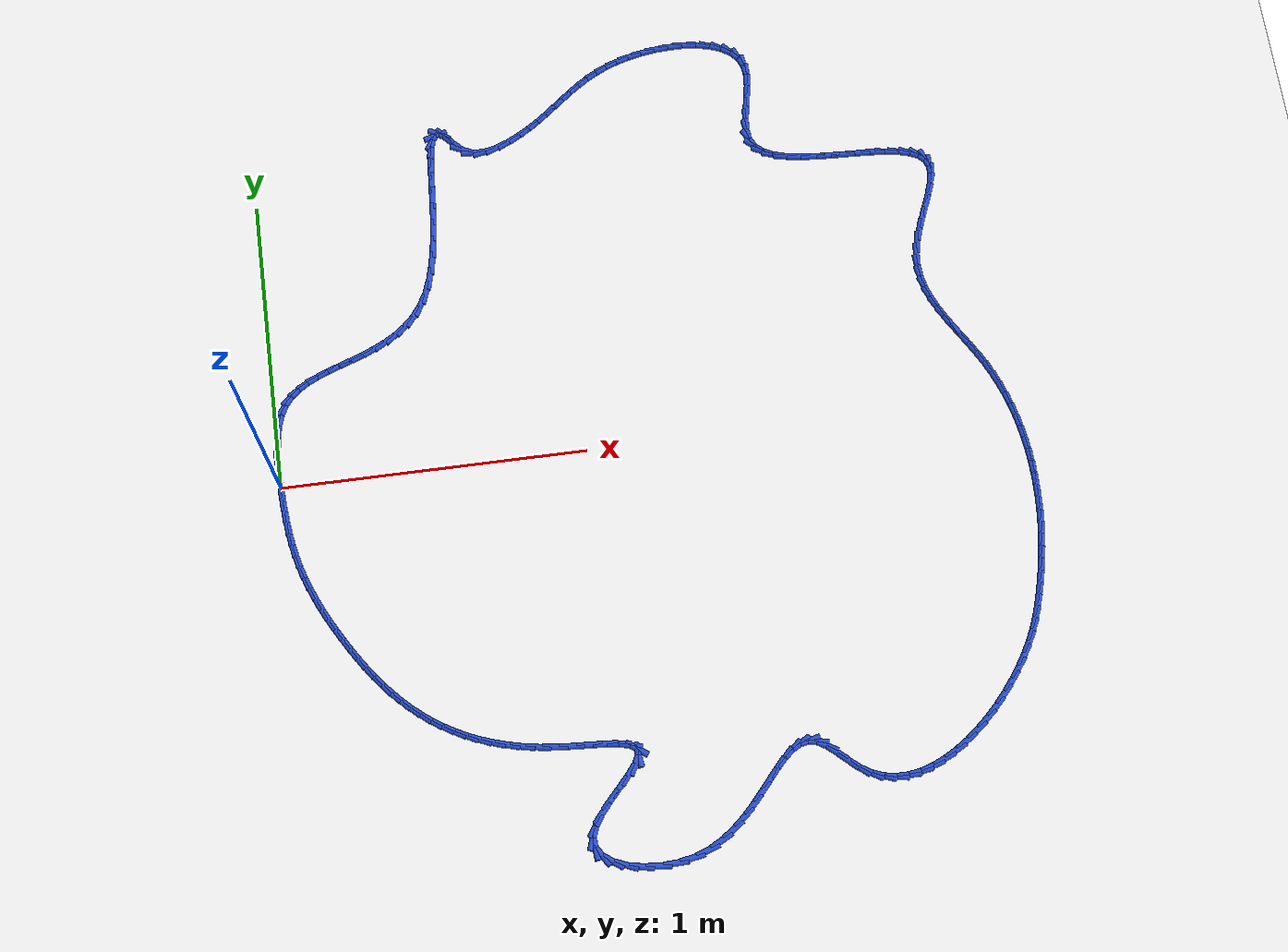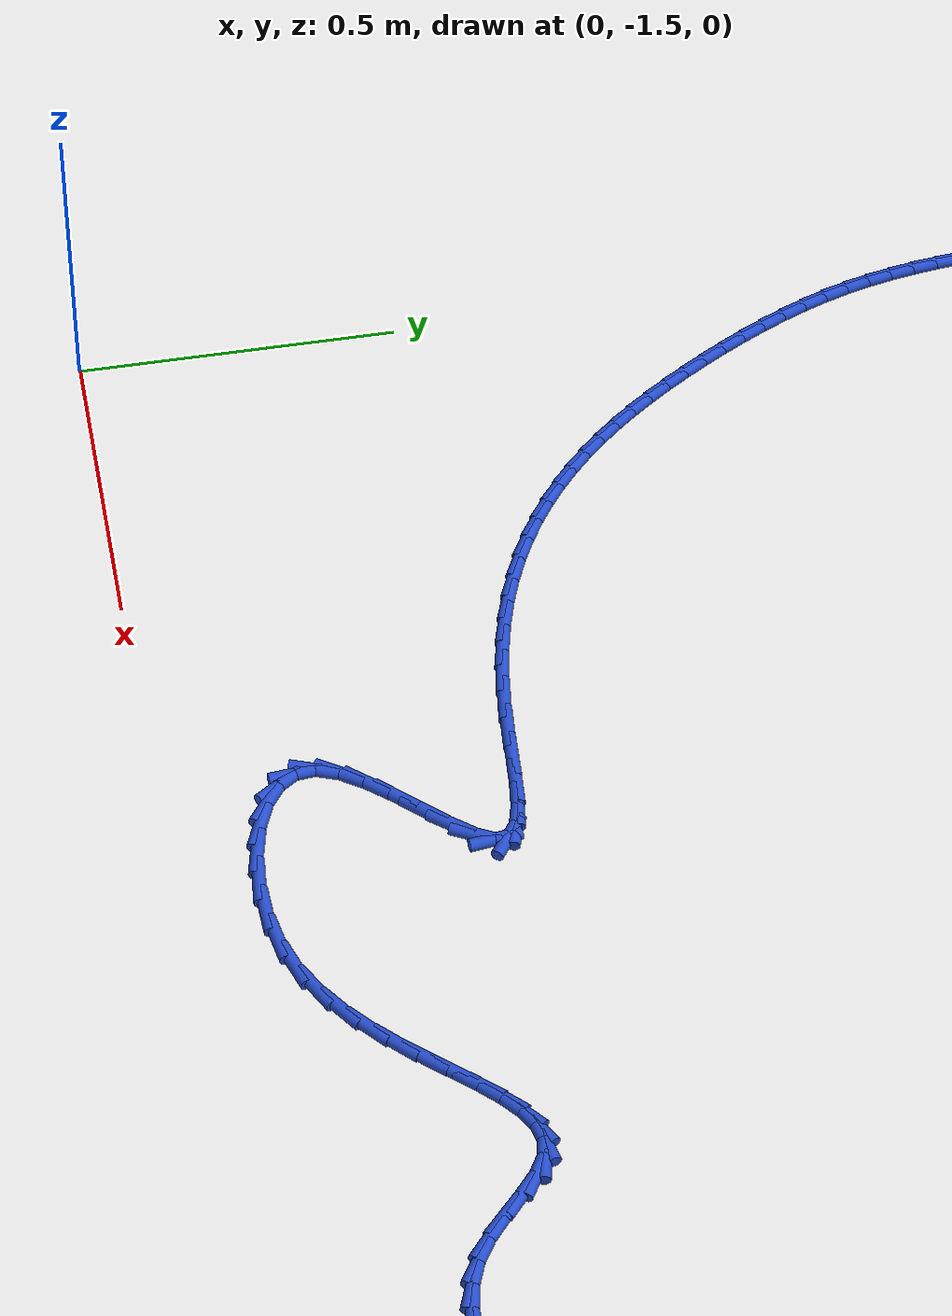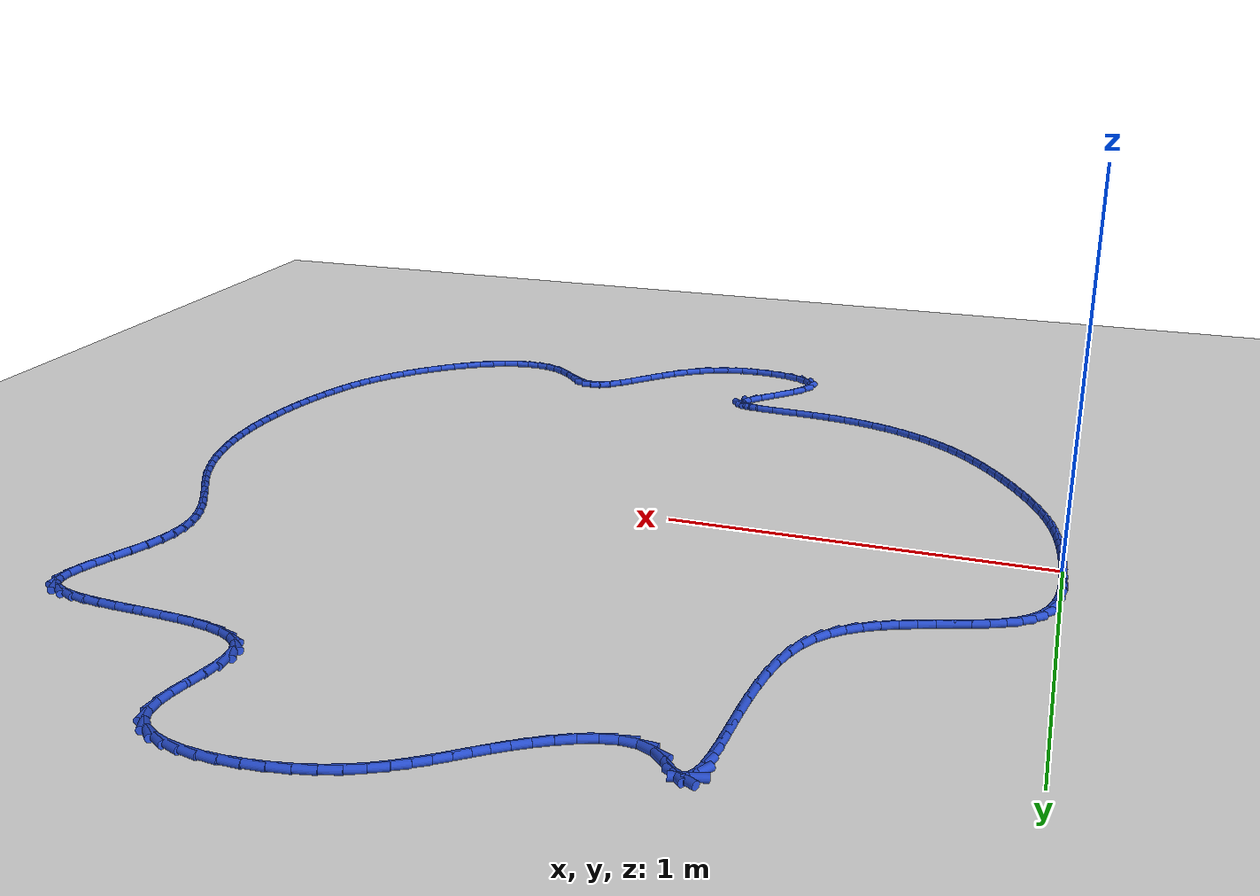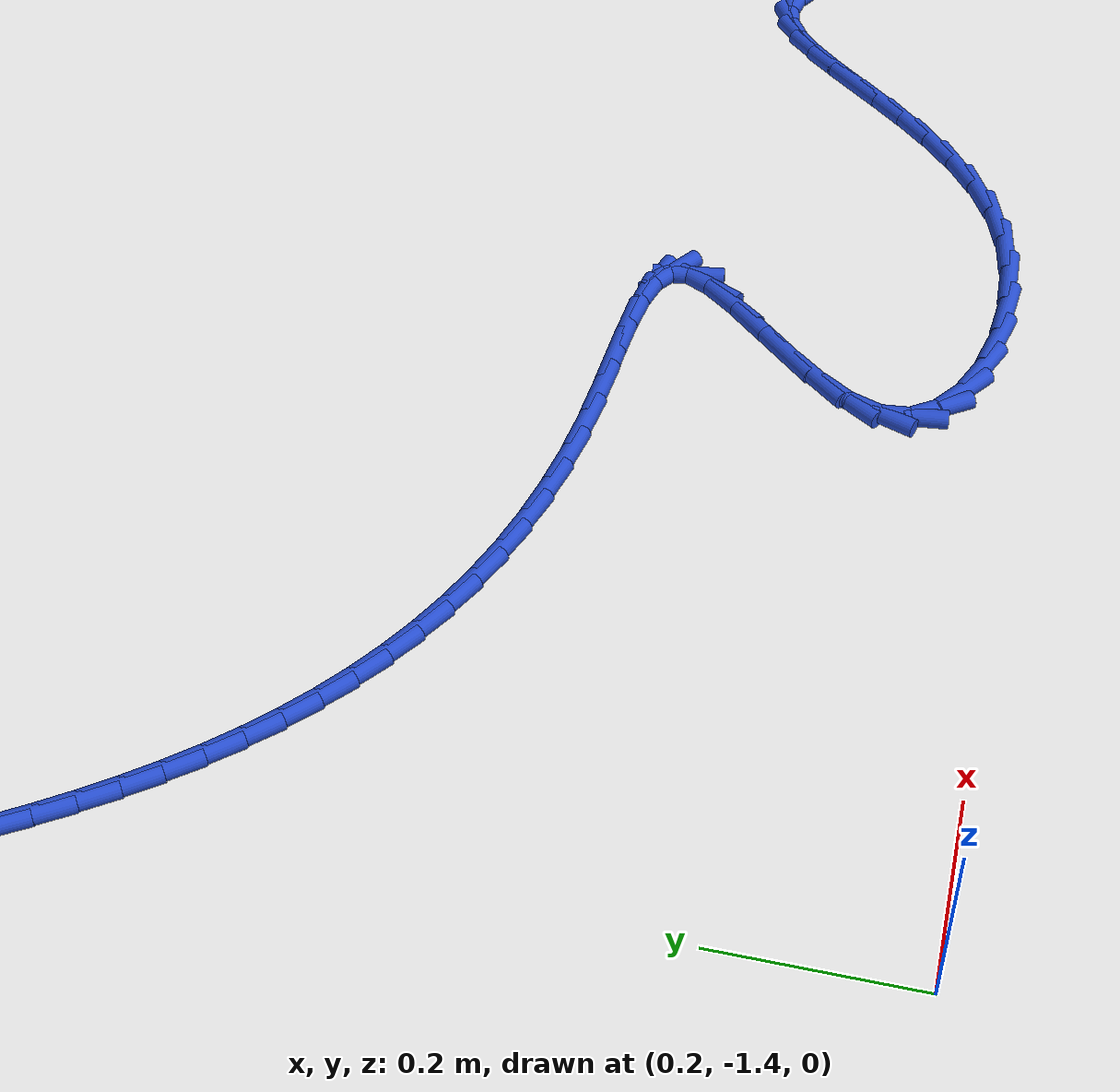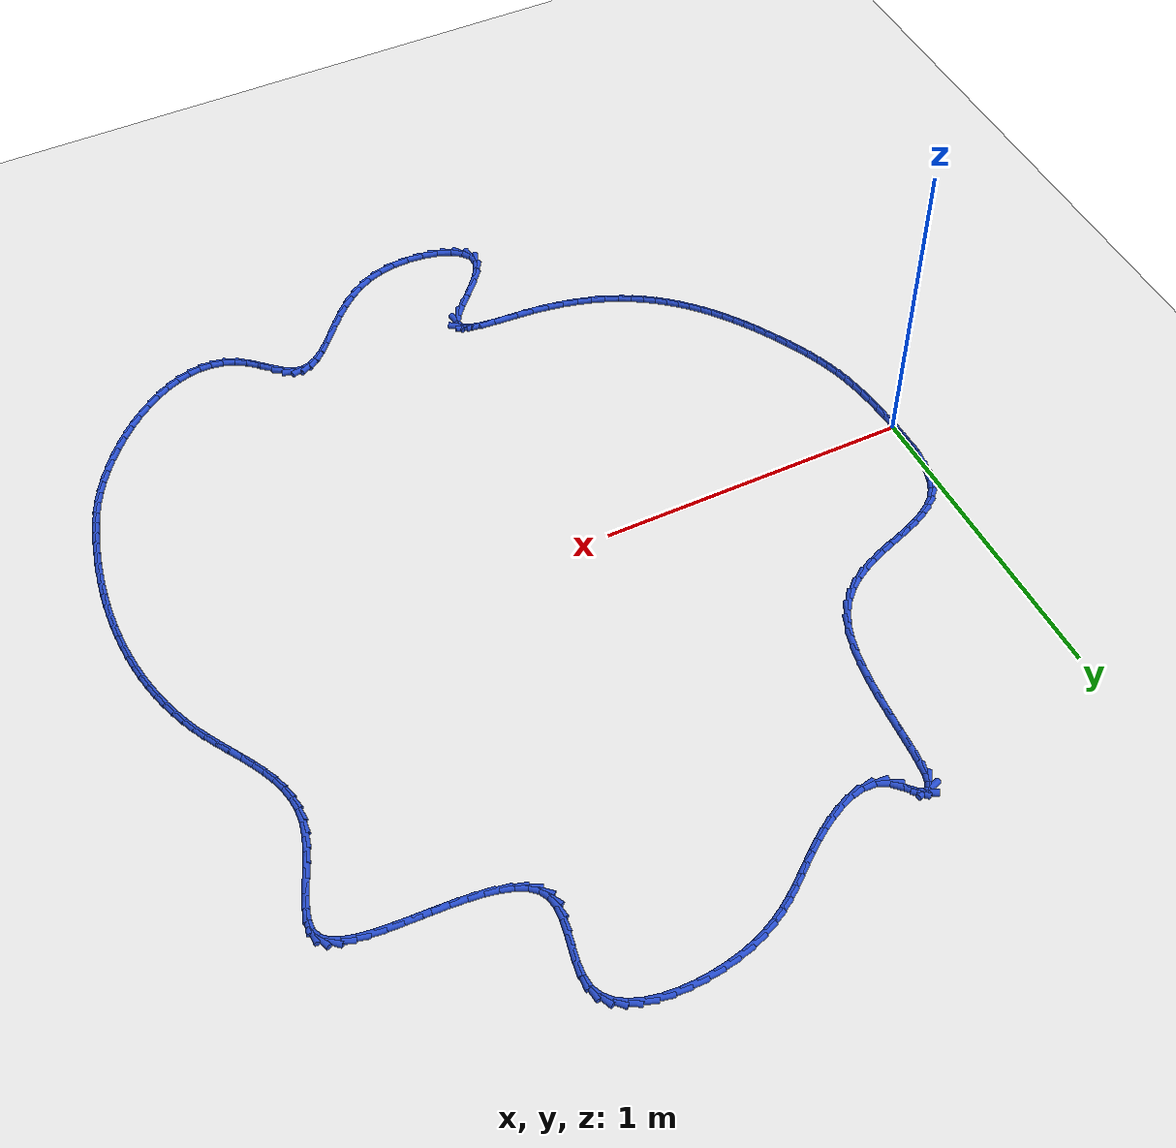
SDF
<sdf version="1.6">
 <world name="default">
  <light name="sun" type="directional">
   <pose>0 0 10 0 -0 0</pose>
   <diffuse>0.8 0.8 0.8 1</diffuse>
   <specular>0.2 0.2 0.2 1</specular>
   <attenuation>
    <range>1000</range>
    <constant>0.9</constant>
    <linear>0.01</linear>
    <quadratic>0.001</quadratic>
   </attenuation>
   <direction>-0.5 0.1 -0.9</direction>
  </light>
  <model name="ground_plane">
   <static>1</static>
   <link name="link">
    <collision name="collision">
     <geometry><plane><normal>0 0 1</normal><size>100 100</size></plane></geometry>
     <surface><friction><ode><mu>100</mu><mu2>50</mu2></ode></friction></surface>
    </collision>
    <visual name="visual">
     <cast_shadows>0</cast_shadows>
     <geometry><plane><normal>0 0 1</normal><size>100 100</size></plane></geometry>
     <material>
      <script><uri>file://media/materials/scripts/gazebo.material</uri><name>Gazebo/WhiteGlow</name></script>
     </material>
    </visual>
   </link>
  </model>
  <gravity>0 0 -9.8</gravity>
  <magnetic_field>6e-06 2.3e-05 -4.2e-05</magnetic_field>
  <atmosphere type="adiabatic"/>
  <physics name="default_physics" default="0" type="ode">
   <max_step_size>0.001</max_step_size>
   <real_time_factor>1</real_time_factor>
   <real_time_update_rate>1000</real_time_update_rate>
  </physics>
  <scene><ambient>0.4 0.4 0.4 1</ambient><background>0.7 0.7 0.7 1</background><shadows>1</shadows></scene>
  <spherical_coordinates>
   <surface_model>EARTH_WGS84</surface_model>
   <latitude_deg>0</latitude_deg>
   <longitude_deg>0</longitude_deg>
   <elevation>0</elevation>
   <heading_deg>0</heading_deg>
  </spherical_coordinates>
  <model name="line">
   <link name="link_0">
    <pose>1.5612511283791264e-17 -2.0816681711721685e-17 0.01 0 1.57 -1.5320196866669449</pose>
    <collision name="collision">
     <geometry><cylinder><radius>0.01</radius><length>0.08</length></cylinder></geometry>
    </collision>
    <visual name="visual">
     <material>
      <script><name>Gazebo/Blue</name><uri>file://media/materials/scripts/gazebo.material</uri></script>
     </material>
     <geometry><cylinder><radius>0.01</radius><length>0.08</length></cylinder></geometry>
    </visual>
   </link>
   <link name="link_1">
    <pose>-0.001676079227338649 0.04320227516199466 0.01 0 1.57 -1.5604415413583341</pose>
    <collision name="collision">
     <geometry><cylinder><radius>0.01</radius><length>0.08</length></cylinder></geometry>
    </collision>
    <visual name="visual">
     <material>
      <script><name>Gazebo/Blue</name><uri>file://media/materials/scripts/gazebo.material</uri></script>
     </material>
     <geometry><cylinder><radius>0.01</radius><length>0.08</length></cylinder></geometry>
    </visual>
   </link>
   <link name="link_2">
    <pose>-0.002126900359094445 0.08673818634214743 0.01 0 1.57 1.5365452437830174</pose>
    <collision name="collision">
     <geometry><cylinder><radius>0.01</radius><length>0.08</length></cylinder></geometry>
    </collision>
    <visual name="visual">
     <material>
      <script><name>Gazebo/Blue</name><uri>file://media/materials/scripts/gazebo.material</uri></script>
     </material>
     <geometry><cylinder><radius>0.01</radius><length>0.08</length></cylinder></geometry>
    </visual>
   </link>
   <link name="link_3">
    <pose>-0.0006539540057294568 0.12972574147044572 0.01 0 1.57 1.4725692312627845</pose>
    <collision name="collision">
     <geometry><cylinder><radius>0.01</radius><length>0.08</length></cylinder></geometry>
    </collision>
    <visual name="visual">
     <material>
      <script><name>Gazebo/Blue</name><uri>file://media/materials/scripts/gazebo.material</uri></script>
     </material>
     <geometry><cylinder><radius>0.01</radius><length>0.08</length></cylinder></geometry>
    </visual>
   </link>
   <link name="link_4">
    <pose>0.003441269222294225 0.17128294847687703 0.01 0 1.57 1.3840309680759006</pose>
    <collision name="collision">
     <geometry><cylinder><radius>0.01</radius><length>0.08</length></cylinder></geometry>
    </collision>
    <visual name="visual">
     <material>
      <script><name>Gazebo/Blue</name><uri>file://media/materials/scripts/gazebo.material</uri></script>
     </material>
     <geometry><cylinder><radius>0.01</radius><length>0.08</length></cylinder></geometry>
    </visual>
   </link>
   <link name="link_5">
    <pose>0.010857278714514525 0.21052781529142867 0.01 0 1.57 1.263633450753926</pose>
    <collision name="collision">
     <geometry><cylinder><radius>0.01</radius><length>0.08</length></cylinder></geometry>
    </collision>
    <visual name="visual">
     <material>
      <script><name>Gazebo/Blue</name><uri>file://media/materials/scripts/gazebo.material</uri></script>
     </material>
     <geometry><cylinder><radius>0.01</radius><length>0.08</length></cylinder></geometry>
    </visual>
   </link>
   <link name="link_6">
    <pose>0.022292583860469346 0.24657834984408805 0.01 0 1.57 1.1030038749452376</pose>
    <collision name="collision">
     <geometry><cylinder><radius>0.01</radius><length>0.08</length></cylinder></geometry>
    </collision>
    <visual name="visual">
     <material>
      <script><name>Gazebo/Blue</name><uri>file://media/materials/scripts/gazebo.material</uri></script>
     </material>
     <geometry><cylinder><radius>0.01</radius><length>0.08</length></cylinder></geometry>
    </visual>
   </link>
   <link name="link_7">
    <pose>0.0384456940496966 0.27855256006484264 0.01 0 1.57 0.904512055702413</pose>
    <collision name="collision">
     <geometry><cylinder><radius>0.01</radius><length>0.08</length></cylinder></geometry>
    </collision>
    <visual name="visual">
     <material>
      <script><name>Gazebo/Blue</name><uri>file://media/materials/scripts/gazebo.material</uri></script>
     </material>
     <geometry><cylinder><radius>0.01</radius><length>0.08</length></cylinder></geometry>
    </visual>
   </link>
   <link name="link_8">
    <pose>0.05984616607619703 0.3057718689551457 0.01 0 1.57 0.7178373368281373</pose>
    <collision name="collision">
     <geometry><cylinder><radius>0.01</radius><length>0.08</length></cylinder></geometry>
    </collision>
    <visual name="visual">
     <material>
      <script><name>Gazebo/Blue</name><uri>file://media/materials/scripts/gazebo.material</uri></script>
     </material>
     <geometry><cylinder><radius>0.01</radius><length>0.08</length></cylinder></geometry>
    </visual>
   </link>
   <link name="link_9">
    <pose>0.08608634790699869 0.328686077567766 0.01 0 1.57 0.5698859152394647</pose>
    <collision name="collision">
     <geometry><cylinder><radius>0.01</radius><length>0.08</length></cylinder></geometry>
    </collision>
    <visual name="visual">
     <material>
      <script><name>Gazebo/Blue</name><uri>file://media/materials/scripts/gazebo.material</uri></script>
     </material>
     <geometry><cylinder><radius>0.01</radius><length>0.08</length></cylinder></geometry>
    </visual>
   </link>
   <link name="link_10">
    <pose>0.11643546304189384 0.348134021444029 0.01 0 1.57 0.4626364875719824</pose>
    <collision name="collision">
     <geometry><cylinder><radius>0.01</radius><length>0.08</length></cylinder></geometry>
    </collision>
    <visual name="visual">
     <material>
      <script><name>Gazebo/Blue</name><uri>file://media/materials/scripts/gazebo.material</uri></script>
     </material>
     <geometry><cylinder><radius>0.01</radius><length>0.08</length></cylinder></geometry>
    </visual>
   </link>
   <link name="link_11">
    <pose>0.1501624326077812 0.3649549001753272 0.01 0 1.57 0.39191305188179215</pose>
    <collision name="collision">
     <geometry><cylinder><radius>0.01</radius><length>0.08</length></cylinder></geometry>
    </collision>
    <visual name="visual">
     <material>
      <script><name>Gazebo/Blue</name><uri>file://media/materials/scripts/gazebo.material</uri></script>
     </material>
     <geometry><cylinder><radius>0.01</radius><length>0.08</length></cylinder></geometry>
    </visual>
   </link>
   <link name="link_12">
    <pose>0.18653617773155967 0.37998791335305304 0.01 0 1.57 0.35247773712628455</pose>
    <collision name="collision">
     <geometry><cylinder><radius>0.01</radius><length>0.08</length></cylinder></geometry>
    </collision>
    <visual name="visual">
     <material>
      <script><name>Gazebo/Blue</name><uri>file://media/materials/scripts/gazebo.material</uri></script>
     </material>
     <geometry><cylinder><radius>0.01</radius><length>0.08</length></cylinder></geometry>
    </visual>
   </link>
   <link name="link_13">
    <pose>0.22482561954012792 0.39407226056859923 0.01 0 1.57 0.3402577865344801</pose>
    <collision name="collision">
     <geometry><cylinder><radius>0.01</radius><length>0.08</length></cylinder></geometry>
    </collision>
    <visual name="visual">
     <material>
      <script><name>Gazebo/Blue</name><uri>file://media/materials/scripts/gazebo.material</uri></script>
     </material>
     <geometry><cylinder><radius>0.01</radius><length>0.08</length></cylinder></geometry>
    </visual>
   </link>
   <link name="link_14">
    <pose>0.2642996791603847 0.40804714141335807 0.01 0 1.57 0.3528679087457212</pose>
    <collision name="collision">
     <geometry><cylinder><radius>0.01</radius><length>0.08</length></cylinder></geometry>
    </collision>
    <visual name="visual">
     <material>
      <script><name>Gazebo/Blue</name><uri>file://media/materials/scripts/gazebo.material</uri></script>
     </material>
     <geometry><cylinder><radius>0.01</radius><length>0.08</length></cylinder></geometry>
    </visual>
   </link>
   <link name="link_15">
    <pose>0.3042272777192289 0.42275175547872207 0.01 0 1.57 0.38946471869403404</pose>
    <collision name="collision">
     <geometry><cylinder><radius>0.01</radius><length>0.08</length></cylinder></geometry>
    </collision>
    <visual name="visual">
     <material>
      <script><name>Gazebo/Blue</name><uri>file://media/materials/scripts/gazebo.material</uri></script>
     </material>
     <geometry><cylinder><radius>0.01</radius><length>0.08</length></cylinder></geometry>
    </visual>
   </link>
   <link name="link_16">
    <pose>0.3438773363435592 0.4390253023560838 0.01 0 1.57 0.4503301331464361</pose>
    <collision name="collision">
     <geometry><cylinder><radius>0.01</radius><length>0.08</length></cylinder></geometry>
    </collision>
    <visual name="visual">
     <material>
      <script><name>Gazebo/Blue</name><uri>file://media/materials/scripts/gazebo.material</uri></script>
     </material>
     <geometry><cylinder><radius>0.01</radius><length>0.08</length></cylinder></geometry>
    </visual>
   </link>
   <link name="link_17">
    <pose>0.3825187761602744 0.45770698163683565 0.01 0 1.57 0.5361838561834372</pose>
    <collision name="collision">
     <geometry><cylinder><radius>0.01</radius><length>0.08</length></cylinder></geometry>
    </collision>
    <visual name="visual">
     <material>
      <script><name>Gazebo/Blue</name><uri>file://media/materials/scripts/gazebo.material</uri></script>
     </material>
     <geometry><cylinder><radius>0.01</radius><length>0.08</length></cylinder></geometry>
    </visual>
   </link>
   <link name="link_18">
    <pose>0.41942051829627314 0.4796359929123704 0.01 0 1.57 0.647066338856265</pose>
    <collision name="collision">
     <geometry><cylinder><radius>0.01</radius><length>0.08</length></cylinder></geometry>
    </collision>
    <visual name="visual">
     <material>
      <script><name>Gazebo/Blue</name><uri>file://media/materials/scripts/gazebo.material</uri></script>
     </material>
     <geometry><cylinder><radius>0.01</radius><length>0.08</length></cylinder></geometry>
    </visual>
   </link>
   <link name="link_19">
    <pose>0.45385148387845453 0.5056515357740803 0.01 0 1.57 0.7807684017649389</pose>
    <collision name="collision">
     <geometry><cylinder><radius>0.01</radius><length>0.08</length></cylinder></geometry>
    </collision>
    <visual name="visual">
     <material>
      <script><name>Gazebo/Blue</name><uri>file://media/materials/scripts/gazebo.material</uri></script>
     </material>
     <geometry><cylinder><radius>0.01</radius><length>0.08</length></cylinder></geometry>
    </visual>
   </link>
   <link name="link_20">
    <pose>0.4850805940337171 0.5365928098133581 0.01 0 1.57 0.9313785206436807</pose>
    <collision name="collision">
     <geometry><cylinder><radius>0.01</radius><length>0.08</length></cylinder></geometry>
    </collision>
    <visual name="visual">
     <material>
      <script><name>Gazebo/Blue</name><uri>file://media/materials/scripts/gazebo.material</uri></script>
     </material>
     <geometry><cylinder><radius>0.01</radius><length>0.08</length></cylinder></geometry>
    </visual>
   </link>
   <link name="link_21">
    <pose>0.5123767698889593 0.5732990146215955 0.01 0 1.57 1.0889362647479612</pose>
    <collision name="collision">
     <geometry><cylinder><radius>0.01</radius><length>0.08</length></cylinder></geometry>
    </collision>
    <visual name="visual">
     <material>
      <script><name>Gazebo/Blue</name><uri>file://media/materials/scripts/gazebo.material</uri></script>
     </material>
     <geometry><cylinder><radius>0.01</radius><length>0.08</length></cylinder></geometry>
    </visual>
   </link>
   <link name="link_22">
    <pose>0.535018539430436 0.616592992482287 0.01 0 1.57 1.227297248713201</pose>
    <collision name="collision">
     <geometry><cylinder><radius>0.01</radius><length>0.08</length></cylinder></geometry>
    </collision>
    <visual name="visual">
     <material>
      <script><name>Gazebo/Blue</name><uri>file://media/materials/scripts/gazebo.material</uri></script>
     </material>
     <geometry><cylinder><radius>0.01</radius><length>0.08</length></cylinder></geometry>
    </visual>
   </link>
   <link name="link_23">
    <pose>0.5528251743252867 0.6663768778226541 0.01 0 1.57 1.3273066975771783</pose>
    <collision name="collision">
     <geometry><cylinder><radius>0.01</radius><length>0.08</length></cylinder></geometry>
    </collision>
    <visual name="visual">
     <material>
      <script><name>Gazebo/Blue</name><uri>file://media/materials/scripts/gazebo.material</uri></script>
     </material>
     <geometry><cylinder><radius>0.01</radius><length>0.08</length></cylinder></geometry>
    </visual>
   </link>
   <link name="link_24">
    <pose>0.5664342089367939 0.7211595740078387 0.01 0 1.57 1.398609026541013</pose>
    <collision name="collision">
     <geometry><cylinder><radius>0.01</radius><length>0.08</length></cylinder></geometry>
    </collision>
    <visual name="visual">
     <material>
      <script><name>Gazebo/Blue</name><uri>file://media/materials/scripts/gazebo.material</uri></script>
     </material>
     <geometry><cylinder><radius>0.01</radius><length>0.08</length></cylinder></geometry>
    </visual>
   </link>
   <link name="link_25">
    <pose>0.5765512913854798 0.7793340091754821 0.01 0 1.57 1.4491371477721249</pose>
    <collision name="collision">
     <geometry><cylinder><radius>0.01</radius><length>0.08</length></cylinder></geometry>
    </collision>
    <visual name="visual">
     <material>
      <script><name>Gazebo/Blue</name><uri>file://media/materials/scripts/gazebo.material</uri></script>
     </material>
     <geometry><cylinder><radius>0.01</radius><length>0.08</length></cylinder></geometry>
    </visual>
   </link>
   <link name="link_26">
    <pose>0.5838820697918662 0.8392931114632254 0.01 0 1.57 1.483713982090917</pose>
    <collision name="collision">
     <geometry><cylinder><radius>0.01</radius><length>0.08</length></cylinder></geometry>
    </collision>
    <visual name="visual">
     <material>
      <script><name>Gazebo/Blue</name><uri>file://media/materials/scripts/gazebo.material</uri></script>
     </material>
     <geometry><cylinder><radius>0.01</radius><length>0.08</length></cylinder></geometry>
    </visual>
   </link>
   <link name="link_27">
    <pose>0.5891321922764753 0.8994298090087095 0.01 0 1.57 1.504884478997767</pose>
    <collision name="collision">
     <geometry><cylinder><radius>0.01</radius><length>0.08</length></cylinder></geometry>
    </collision>
    <visual name="visual">
     <material>
      <script><name>Gazebo/Blue</name><uri>file://media/materials/scripts/gazebo.material</uri></script>
     </material>
     <geometry><cylinder><radius>0.01</radius><length>0.08</length></cylinder></geometry>
    </visual>
   </link>
   <link name="link_28">
    <pose>0.5930073069598291 0.9581370299495756 0.01 0 1.57 1.5132755798546838</pose>
    <collision name="collision">
     <geometry><cylinder><radius>0.01</radius><length>0.08</length></cylinder></geometry>
    </collision>
    <visual name="visual">
     <material>
      <script><name>Gazebo/Blue</name><uri>file://media/materials/scripts/gazebo.material</uri></script>
     </material>
     <geometry><cylinder><radius>0.01</radius><length>0.08</length></cylinder></geometry>
    </visual>
   </link>
   <link name="link_29">
    <pose>0.5962130619624496 1.0138077024234649 0.01 0 1.57 1.5073458362425172</pose>
    <collision name="collision">
     <geometry><cylinder><radius>0.01</radius><length>0.08</length></cylinder></geometry>
    </collision>
    <visual name="visual">
     <material>
      <script><name>Gazebo/Blue</name><uri>file://media/materials/scripts/gazebo.material</uri></script>
     </material>
     <geometry><cylinder><radius>0.01</radius><length>0.08</length></cylinder></geometry>
    </visual>
   </link>
   <link name="link_30">
    <pose>0.5994551054048587 1.0648347545680181 0.01 0 1.57 1.4820549347129033</pose>
    <collision name="collision">
     <geometry><cylinder><radius>0.01</radius><length>0.08</length></cylinder></geometry>
    </collision>
    <visual name="visual">
     <material>
      <script><name>Gazebo/Blue</name><uri>file://media/materials/scripts/gazebo.material</uri></script>
     </material>
     <geometry><cylinder><radius>0.01</radius><length>0.08</length></cylinder></geometry>
    </visual>
   </link>
   <link name="link_31">
    <pose>0.6034390854075785 1.1096111145208762 0.01 0 1.57 1.4247215142123222</pose>
    <collision name="collision">
     <geometry><cylinder><radius>0.01</radius><length>0.08</length></cylinder></geometry>
    </collision>
    <visual name="visual">
     <material>
      <script><name>Gazebo/Blue</name><uri>file://media/materials/scripts/gazebo.material</uri></script>
     </material>
     <geometry><cylinder><radius>0.01</radius><length>0.08</length></cylinder></geometry>
    </visual>
   </link>
   <link name="link_32">
    <pose>0.6088706500911311 1.146529710419681 0.01 0 1.57 1.3012448087792454</pose>
    <collision name="collision">
     <geometry><cylinder><radius>0.01</radius><length>0.08</length></cylinder></geometry>
    </collision>
    <visual name="visual">
     <material>
      <script><name>Gazebo/Blue</name><uri>file://media/materials/scripts/gazebo.material</uri></script>
     </material>
     <geometry><cylinder><radius>0.01</radius><length>0.08</length></cylinder></geometry>
    </visual>
   </link>
   <link name="link_33">
    <pose>0.6164554475760384 1.1739834704020728 0.01 0 1.57 1.0032479541702728</pose>
    <collision name="collision">
     <geometry><cylinder><radius>0.01</radius><length>0.08</length></cylinder></geometry>
    </collision>
    <visual name="visual">
     <material>
      <script><name>Gazebo/Blue</name><uri>file://media/materials/scripts/gazebo.material</uri></script>
     </material>
     <geometry><cylinder><radius>0.01</radius><length>0.08</length></cylinder></geometry>
    </visual>
   </link>
   <link name="link_34">
    <pose>0.6268991259828225 1.1903653226056932 0.01 0 1.57 0.2584251340858222</pose>
    <collision name="collision">
     <geometry><cylinder><radius>0.01</radius><length>0.08</length></cylinder></geometry>
    </collision>
    <visual name="visual">
     <material>
      <script><name>Gazebo/Blue</name><uri>file://media/materials/scripts/gazebo.material</uri></script>
     </material>
     <geometry><cylinder><radius>0.01</radius><length>0.08</length></cylinder></geometry>
    </visual>
   </link>
   <link name="link_35">
    <pose>0.6409073334320056 1.194068195168183 0.01 0 1.57 -0.5248349542645053</pose>
    <collision name="collision">
     <geometry><cylinder><radius>0.01</radius><length>0.08</length></cylinder></geometry>
    </collision>
    <visual name="visual">
     <material>
      <script><name>Gazebo/Blue</name><uri>file://media/materials/scripts/gazebo.material</uri></script>
     </material>
     <geometry><cylinder><radius>0.01</radius><length>0.08</length></cylinder></geometry>
    </visual>
   </link>
   <link name="link_36">
    <pose>0.6591857180441094 1.1834850162271835 0.01 0 1.57 -0.8353414293036994</pose>
    <collision name="collision">
     <geometry><cylinder><radius>0.01</radius><length>0.08</length></cylinder></geometry>
    </collision>
    <visual name="visual">
     <material>
      <script><name>Gazebo/Blue</name><uri>file://media/materials/scripts/gazebo.material</uri></script>
     </material>
     <geometry><cylinder><radius>0.01</radius><length>0.08</length></cylinder></geometry>
    </visual>
   </link>
   <link name="link_37">
    <pose>0.6824433980080781 1.1577799411605774 0.01 0 1.57 -0.798774468301952</pose>
    <collision name="collision">
     <geometry><cylinder><radius>0.01</radius><length>0.08</length></cylinder></geometry>
    </collision>
    <visual name="visual">
     <material>
      <script><name>Gazebo/Blue</name><uri>file://media/materials/scripts/gazebo.material</uri></script>
     </material>
     <geometry><cylinder><radius>0.01</radius><length>0.08</length></cylinder></geometry>
    </visual>
   </link>
   <link name="link_38">
    <pose>0.7114429305881919 1.1279940296547748 0.01 0 1.57 -0.4415822130064496</pose>
    <collision name="collision">
     <geometry><cylinder><radius>0.01</radius><length>0.08</length></cylinder></geometry>
    </collision>
    <visual name="visual">
     <material>
      <script><name>Gazebo/Blue</name><uri>file://media/materials/scripts/gazebo.material</uri></script>
     </material>
     <geometry><cylinder><radius>0.01</radius><length>0.08</length></cylinder></geometry>
    </visual>
   </link>
   <link name="link_39">
    <pose>0.7465913583304427 1.1113788457166782 0.01 0 1.57 -0.049692923586918014</pose>
    <collision name="collision">
     <geometry><cylinder><radius>0.01</radius><length>0.08</length></cylinder></geometry>
    </collision>
    <visual name="visual">
     <material>
      <script><name>Gazebo/Blue</name><uri>file://media/materials/scripts/gazebo.material</uri></script>
     </material>
     <geometry><cylinder><radius>0.01</radius><length>0.08</length></cylinder></geometry>
    </visual>
   </link>
   <link name="link_40">
    <pose>0.7862469737587642 1.109406618584971 0.01 0 1.57 0.2115407290617461</pose>
    <collision name="collision">
     <geometry><cylinder><radius>0.01</radius><length>0.08</length></cylinder></geometry>
    </collision>
    <visual name="visual">
     <material>
      <script><name>Gazebo/Blue</name><uri>file://media/materials/scripts/gazebo.material</uri></script>
     </material>
     <geometry><cylinder><radius>0.01</radius><length>0.08</length></cylinder></geometry>
    </visual>
   </link>
   <link name="link_41">
    <pose>0.8281091035186868 1.1183966657867228 0.01 0 1.57 0.37143662166341423</pose>
    <collision name="collision">
     <geometry><cylinder><radius>0.01</radius><length>0.08</length></cylinder></geometry>
    </collision>
    <visual name="visual">
     <material>
      <script><name>Gazebo/Blue</name><uri>file://media/materials/scripts/gazebo.material</uri></script>
     </material>
     <geometry><cylinder><radius>0.01</radius><length>0.08</length></cylinder></geometry>
    </visual>
   </link>
   <link name="link_42">
    <pose>0.8698767631484277 1.1346658720849254 0.01 0 1.57 0.46797613083560824</pose>
    <collision name="collision">
     <geometry><cylinder><radius>0.01</radius><length>0.08</length></cylinder></geometry>
    </collision>
    <visual name="visual">
     <material>
      <script><name>Gazebo/Blue</name><uri>file://media/materials/scripts/gazebo.material</uri></script>
     </material>
     <geometry><cylinder><radius>0.01</radius><length>0.08</length></cylinder></geometry>
    </visual>
   </link>
   <link name="link_43">
    <pose>0.9093059677840348 1.1545942761773187 0.01 0 1.57 0.5357757117277205</pose>
    <collision name="collision">
     <geometry><cylinder><radius>0.01</radius><length>0.08</length></cylinder></geometry>
    </collision>
    <visual name="visual">
     <material>
      <script><name>Gazebo/Blue</name><uri>file://media/materials/scripts/gazebo.material</uri></script>
     </material>
     <geometry><cylinder><radius>0.01</radius><length>0.08</length></cylinder></geometry>
    </visual>
   </link>
   <link name="link_44">
    <pose>0.9455546267833702 1.1761151757244634 0.01 0 1.57 0.5921940402596497</pose>
    <collision name="collision">
     <geometry><cylinder><radius>0.01</radius><length>0.08</length></cylinder></geometry>
    </collision>
    <visual name="visual">
     <material>
      <script><name>Gazebo/Blue</name><uri>file://media/materials/scripts/gazebo.material</uri></script>
     </material>
     <geometry><cylinder><radius>0.01</radius><length>0.08</length></cylinder></geometry>
    </visual>
   </link>
   <link name="link_45">
    <pose>0.9792349863080558 1.1987732322403784 0.01 0 1.57 0.634804874455717</pose>
    <collision name="collision">
     <geometry><cylinder><radius>0.01</radius><length>0.08</length></cylinder></geometry>
    </collision>
    <visual name="visual">
     <material>
      <script><name>Gazebo/Blue</name><uri>file://media/materials/scripts/gazebo.material</uri></script>
     </material>
     <geometry><cylinder><radius>0.01</radius><length>0.08</length></cylinder></geometry>
    </visual>
   </link>
   <link name="link_46">
    <pose>1.0110267850688366 1.2221878870657032 0.01 0 1.57 0.6611233290945785</pose>
    <collision name="collision">
     <geometry><cylinder><radius>0.01</radius><length>0.08</length></cylinder></geometry>
    </collision>
    <visual name="visual">
     <material>
      <script><name>Gazebo/Blue</name><uri>file://media/materials/scripts/gazebo.material</uri></script>
     </material>
     <geometry><cylinder><radius>0.01</radius><length>0.08</length></cylinder></geometry>
    </visual>
   </link>
   <link name="link_47">
    <pose>1.0416097617764586 1.2459785815410784 0.01 0 1.57 0.6695061817261639</pose>
    <collision name="collision">
     <geometry><cylinder><radius>0.01</radius><length>0.08</length></cylinder></geometry>
    </collision>
    <visual name="visual">
     <material>
      <script><name>Gazebo/Blue</name><uri>file://media/materials/scripts/gazebo.material</uri></script>
     </material>
     <geometry><cylinder><radius>0.01</radius><length>0.08</length></cylinder></geometry>
    </visual>
   </link>
   <link name="link_48">
    <pose>1.0716636551416667 1.2697647570071444 0.01 0 1.57 0.6591564189813733</pose>
    <collision name="collision">
     <geometry><cylinder><radius>0.01</radius><length>0.08</length></cylinder></geometry>
    </collision>
    <visual name="visual">
     <material>
      <script><name>Gazebo/Blue</name><uri>file://media/materials/scripts/gazebo.material</uri></script>
     </material>
     <geometry><cylinder><radius>0.01</radius><length>0.08</length></cylinder></geometry>
    </visual>
   </link>
   <link name="link_49">
    <pose>1.101868203875207 1.293165854804542 0.01 0 1.57 0.6301562417405734</pose>
    <collision name="collision">
     <geometry><cylinder><radius>0.01</radius><length>0.08</length></cylinder></geometry>
    </collision>
    <visual name="visual">
     <material>
      <script><name>Gazebo/Blue</name><uri>file://media/materials/scripts/gazebo.material</uri></script>
     </material>
     <geometry><cylinder><radius>0.01</radius><length>0.08</length></cylinder></geometry>
    </visual>
   </link>
   <link name="link_50">
    <pose>1.1329031466878245 1.3158013162739106 0.01 0 1.57 0.5835766661697965</pose>
    <collision name="collision">
     <geometry><cylinder><radius>0.01</radius><length>0.08</length></cylinder></geometry>
    </collision>
    <visual name="visual">
     <material>
      <script><name>Gazebo/Blue</name><uri>file://media/materials/scripts/gazebo.material</uri></script>
     </material>
     <geometry><cylinder><radius>0.01</radius><length>0.08</length></cylinder></geometry>
    </visual>
   </link>
   <link name="link_51">
    <pose>1.1654482222902647 1.337290582755891 0.01 0 1.57 0.5216161233795654</pose>
    <collision name="collision">
     <geometry><cylinder><radius>0.01</radius><length>0.08</length></cylinder></geometry>
    </collision>
    <visual name="visual">
     <material>
      <script><name>Gazebo/Blue</name><uri>file://media/materials/scripts/gazebo.material</uri></script>
     </material>
     <geometry><cylinder><radius>0.01</radius><length>0.08</length></cylinder></geometry>
    </visual>
   </link>
   <link name="link_52">
    <pose>1.2001831693932727 1.3572530955911235 0.01 0 1.57 0.4476283154227192</pose>
    <collision name="collision">
     <geometry><cylinder><radius>0.01</radius><length>0.08</length></cylinder></geometry>
    </collision>
    <visual name="visual">
     <material>
      <script><name>Gazebo/Blue</name><uri>file://media/materials/scripts/gazebo.material</uri></script>
     </material>
     <geometry><cylinder><radius>0.01</radius><length>0.08</length></cylinder></geometry>
    </visual>
   </link>
   <link name="link_53">
    <pose>1.2377877267075943 1.3753082961202483 0.01 0 1.57 0.36587993217432146</pose>
    <collision name="collision">
     <geometry><cylinder><radius>0.01</radius><length>0.08</length></cylinder></geometry>
    </collision>
    <visual name="visual">
     <material>
      <script><name>Gazebo/Blue</name><uri>file://media/materials/scripts/gazebo.material</uri></script>
     </material>
     <geometry><cylinder><radius>0.01</radius><length>0.08</length></cylinder></geometry>
    </visual>
   </link>
   <link name="link_54">
    <pose>1.2789416327303853 1.391075625690705 0.01 0 1.57 0.28325678365939105</pose>
    <collision name="collision">
     <geometry><cylinder><radius>0.01</radius><length>0.08</length></cylinder></geometry>
    </collision>
    <visual name="visual">
     <material>
      <script><name>Gazebo/Blue</name><uri>file://media/materials/scripts/gazebo.material</uri></script>
     </material>
     <geometry><cylinder><radius>0.01</radius><length>0.08</length></cylinder></geometry>
    </visual>
   </link>
   <link name="link_55">
    <pose>1.3239797992044735 1.4041855028396157 0.01 0 1.57 0.20826863636165976</pose>
    <collision name="collision">
     <geometry><cylinder><radius>0.01</radius><length>0.08</length></cylinder></geometry>
    </collision>
    <visual name="visual">
     <material>
      <script><name>Gazebo/Blue</name><uri>file://media/materials/scripts/gazebo.material</uri></script>
     </material>
     <geometry><cylinder><radius>0.01</radius><length>0.08</length></cylinder></geometry>
    </visual>
   </link>
   <link name="link_56">
    <pose>1.3718929490592258 1.414311136912495 0.01 0 1.57 0.13714847889465667</pose>
    <collision name="collision">
     <geometry><cylinder><radius>0.01</radius><length>0.08</length></cylinder></geometry>
    </collision>
    <visual name="visual">
     <material>
      <script><name>Gazebo/Blue</name><uri>file://media/materials/scripts/gazebo.material</uri></script>
     </material>
     <geometry><cylinder><radius>0.01</radius><length>0.08</length></cylinder></geometry>
    </visual>
   </link>
   <link name="link_57">
    <pose>1.421344315159865 1.4211361625496135 0.01 0 1.57 0.06451998881389966</pose>
    <collision name="collision">
     <geometry><cylinder><radius>0.01</radius><length>0.08</length></cylinder></geometry>
    </collision>
    <visual name="visual">
     <material>
      <script><name>Gazebo/Blue</name><uri>file://media/materials/scripts/gazebo.material</uri></script>
     </material>
     <geometry><cylinder><radius>0.01</radius><length>0.08</length></cylinder></geometry>
    </visual>
   </link>
   <link name="link_58">
    <pose>1.4709971303716098 1.4243442143912395 0.01 0 1.57 -0.014947871091928031</pose>
    <collision name="collision">
     <geometry><cylinder><radius>0.01</radius><length>0.08</length></cylinder></geometry>
    </collision>
    <visual name="visual">
     <material>
      <script><name>Gazebo/Blue</name><uri>file://media/materials/scripts/gazebo.material</uri></script>
     </material>
     <geometry><cylinder><radius>0.01</radius><length>0.08</length></cylinder></geometry>
    </visual>
   </link>
   <link name="link_59">
    <pose>1.519514627559683 1.4236189270776434 0.01 0 1.57 -0.10762781949264737</pose>
    <collision name="collision">
     <geometry><cylinder><radius>0.01</radius><length>0.08</length></cylinder></geometry>
    </collision>
    <visual name="visual">
     <material>
      <script><name>Gazebo/Blue</name><uri>file://media/materials/scripts/gazebo.material</uri></script>
     </material>
     <geometry><cylinder><radius>0.01</radius><length>0.08</length></cylinder></geometry>
    </visual>
   </link>
   <link name="link_60">
    <pose>1.5655600395893052 1.4186439352490954 0.01 0 1.57 -0.22216691962087345</pose>
    <collision name="collision">
     <geometry><cylinder><radius>0.01</radius><length>0.08</length></cylinder></geometry>
    </collision>
    <visual name="visual">
     <material>
      <script><name>Gazebo/Blue</name><uri>file://media/materials/scripts/gazebo.material</uri></script>
     </material>
     <geometry><cylinder><radius>0.01</radius><length>0.08</length></cylinder></geometry>
    </visual>
   </link>
   <link name="link_61">
    <pose>1.6077965993256975 1.4091028735458642 0.01 0 1.57 -0.37087354583040577</pose>
    <collision name="collision">
     <geometry><cylinder><radius>0.01</radius><length>0.08</length></cylinder></geometry>
    </collision>
    <visual name="visual">
     <material>
      <script><name>Gazebo/Blue</name><uri>file://media/materials/scripts/gazebo.material</uri></script>
     </material>
     <geometry><cylinder><radius>0.01</radius><length>0.08</length></cylinder></geometry>
    </visual>
   </link>
   <link name="link_62">
    <pose>1.6448875396340805 1.3946793766082195 0.01 0 1.57 -0.5700735696764705</pose>
    <collision name="collision">
     <geometry><cylinder><radius>0.01</radius><length>0.08</length></cylinder></geometry>
    </collision>
    <visual name="visual">
     <material>
      <script><name>Gazebo/Blue</name><uri>file://media/materials/scripts/gazebo.material</uri></script>
     </material>
     <geometry><cylinder><radius>0.01</radius><length>0.08</length></cylinder></geometry>
    </visual>
   </link>
   <link name="link_63">
    <pose>1.6754960933796759 1.3750570790764312 0.01 0 1.57 -0.8343516583037315</pose>
    <collision name="collision">
     <geometry><cylinder><radius>0.01</radius><length>0.08</length></cylinder></geometry>
    </collision>
    <visual name="visual">
     <material>
      <script><name>Gazebo/Blue</name><uri>file://media/materials/scripts/gazebo.material</uri></script>
     </material>
     <geometry><cylinder><radius>0.01</radius><length>0.08</length></cylinder></geometry>
    </visual>
   </link>
   <link name="link_64">
    <pose>1.6982854934277045 1.3499196155907696 0.01 0 1.57 -1.1560919919292252</pose>
    <collision name="collision">
     <geometry><cylinder><radius>0.01</radius><length>0.08</length></cylinder></geometry>
    </collision>
    <visual name="visual">
     <material>
      <script><name>Gazebo/Blue</name><uri>file://media/materials/scripts/gazebo.material</uri></script>
     </material>
     <geometry><cylinder><radius>0.01</radius><length>0.08</length></cylinder></geometry>
    </visual>
   </link>
   <link name="link_65">
    <pose>1.7119191188033827 1.318950693500428 0.01 0 1.57 -1.4624965007417594</pose>
    <collision name="collision">
     <geometry><cylinder><radius>0.01</radius><length>0.08</length></cylinder></geometry>
    </collision>
    <visual name="visual">
     <material>
      <script><name>Gazebo/Blue</name><uri>file://media/materials/scripts/gazebo.material</uri></script>
     </material>
     <geometry><cylinder><radius>0.01</radius><length>0.08</length></cylinder></geometry>
    </visual>
   </link>
   <link name="link_66">
    <pose>1.7159087505874528 1.282256067249752 0.01 0 1.57 1.4903596662822713</pose>
    <collision name="collision">
     <geometry><cylinder><radius>0.01</radius><length>0.08</length></cylinder></geometry>
    </collision>
    <visual name="visual">
     <material>
      <script><name>Gazebo/Blue</name><uri>file://media/materials/scripts/gazebo.material</uri></script>
     </material>
     <geometry><cylinder><radius>0.01</radius><length>0.08</length></cylinder></geometry>
    </visual>
   </link>
   <link name="link_67">
    <pose>1.7126118618357997 1.2413571125960923 0.01 0 1.57 1.3963177285786905</pose>
    <collision name="collision">
     <geometry><cylinder><radius>0.01</radius><length>0.08</length></cylinder></geometry>
    </collision>
    <visual name="visual">
     <material>
      <script><name>Gazebo/Blue</name><uri>file://media/materials/scripts/gazebo.material</uri></script>
     </material>
     <geometry><cylinder><radius>0.01</radius><length>0.08</length></cylinder></geometry>
    </visual>
   </link>
   <link name="link_68">
    <pose>1.7049818964414296 1.1980716776579436 0.01 0 1.57 1.3681707289335718</pose>
    <collision name="collision">
     <geometry><cylinder><radius>0.01</radius><length>0.08</length></cylinder></geometry>
    </collision>
    <visual name="visual">
     <material>
      <script><name>Gazebo/Blue</name><uri>file://media/materials/scripts/gazebo.material</uri></script>
     </material>
     <geometry><cylinder><radius>0.01</radius><length>0.08</length></cylinder></geometry>
    </visual>
   </link>
   <link name="link_69">
    <pose>1.6959722982973509 1.1542176105538025 0.01 0 1.57 1.3980075887196655</pose>
    <collision name="collision">
     <geometry><cylinder><radius>0.01</radius><length>0.08</length></cylinder></geometry>
    </collision>
    <visual name="visual">
     <material>
      <script><name>Gazebo/Blue</name><uri>file://media/materials/scripts/gazebo.material</uri></script>
     </material>
     <geometry><cylinder><radius>0.01</radius><length>0.08</length></cylinder></geometry>
    </visual>
   </link>
   <link name="link_70">
    <pose>1.6885365112965702 1.1116127594021636 0.01 0 1.57 1.4973652478801267</pose>
    <collision name="collision">
     <geometry><cylinder><radius>0.01</radius><length>0.08</length></cylinder></geometry>
    </collision>
    <visual name="visual">
     <material>
      <script><name>Gazebo/Blue</name><uri>file://media/materials/scripts/gazebo.material</uri></script>
     </material>
     <geometry><cylinder><radius>0.01</radius><length>0.08</length></cylinder></geometry>
    </visual>
   </link>
   <link name="link_71">
    <pose>1.6856279793320958 1.0720749723215237 0.01 0 1.57 -1.4396121487080695</pose>
    <collision name="collision">
     <geometry><cylinder><radius>0.01</radius><length>0.08</length></cylinder></geometry>
    </collision>
    <visual name="visual">
     <material>
      <script><name>Gazebo/Blue</name><uri>file://media/materials/scripts/gazebo.material</uri></script>
     </material>
     <geometry><cylinder><radius>0.01</radius><length>0.08</length></cylinder></geometry>
    </visual>
   </link>
   <link name="link_72">
    <pose>1.690200146296934 1.0374220974303767 0.01 0 1.57 -1.0935645309023976</pose>
    <collision name="collision">
     <geometry><cylinder><radius>0.01</radius><length>0.08</length></cylinder></geometry>
    </collision>
    <visual name="visual">
     <material>
      <script><name>Gazebo/Blue</name><uri>file://media/materials/scripts/gazebo.material</uri></script>
     </material>
     <geometry><cylinder><radius>0.01</radius><length>0.08</length></cylinder></geometry>
    </visual>
   </link>
   <link name="link_73">
    <pose>1.7047857624948868 1.0092153885105788 0.01 0 1.57 -0.7335880757900309</pose>
    <collision name="collision">
     <geometry><cylinder><radius>0.01</radius><length>0.08</length></cylinder></geometry>
    </collision>
    <visual name="visual">
     <material>
      <script><name>Gazebo/Blue</name><uri>file://media/materials/scripts/gazebo.material</uri></script>
     </material>
     <geometry><cylinder><radius>0.01</radius><length>0.08</length></cylinder></geometry>
    </visual>
   </link>
   <link name="link_74">
    <pose>1.7291006380055527 0.9872979583341555 0.01 0 1.57 -0.4682707206913578</pose>
    <collision name="collision">
     <geometry><cylinder><radius>0.01</radius><length>0.08</length></cylinder></geometry>
    </collision>
    <visual name="visual">
     <material>
      <script><name>Gazebo/Blue</name><uri>file://media/materials/scripts/gazebo.material</uri></script>
     </material>
     <geometry><cylinder><radius>0.01</radius><length>0.08</length></cylinder></geometry>
    </visual>
   </link>
   <link name="link_75">
    <pose>1.761703950775782 0.9708074531234767 0.01 0 1.57 -0.2936385508577493</pose>
    <collision name="collision">
     <geometry><cylinder><radius>0.01</radius><length>0.08</length></cylinder></geometry>
    </collision>
    <visual name="visual">
     <material>
      <script><name>Gazebo/Blue</name><uri>file://media/materials/scripts/gazebo.material</uri></script>
     </material>
     <geometry><cylinder><radius>0.01</radius><length>0.08</length></cylinder></geometry>
    </visual>
   </link>
   <link name="link_76">
    <pose>1.8011513440065663 0.9588793631475234 0.01 0 1.57 -0.181496947684952</pose>
    <collision name="collision">
     <geometry><cylinder><radius>0.01</radius><length>0.08</length></cylinder></geometry>
    </collision>
    <visual name="visual">
     <material>
      <script><name>Gazebo/Blue</name><uri>file://media/materials/scripts/gazebo.material</uri></script>
     </material>
     <geometry><cylinder><radius>0.01</radius><length>0.08</length></cylinder></geometry>
    </visual>
   </link>
   <link name="link_77">
    <pose>1.8459984608988944 0.9506491786752759 0.01 0 1.57 -0.1101368084974789</pose>
    <collision name="collision">
     <geometry><cylinder><radius>0.01</radius><length>0.08</length></cylinder></geometry>
    </collision>
    <visual name="visual">
     <material>
      <script><name>Gazebo/Blue</name><uri>file://media/materials/scripts/gazebo.material</uri></script>
     </material>
     <geometry><cylinder><radius>0.01</radius><length>0.08</length></cylinder></geometry>
    </visual>
   </link>
   <link name="link_78">
    <pose>1.8948009446537577 0.9452523899757155 0.01 0 1.57 -0.06670403485473357</pose>
    <collision name="collision">
     <geometry><cylinder><radius>0.01</radius><length>0.08</length></cylinder></geometry>
    </collision>
    <visual name="visual">
     <material>
      <script><name>Gazebo/Blue</name><uri>file://media/materials/scripts/gazebo.material</uri></script>
     </material>
     <geometry><cylinder><radius>0.01</radius><length>0.08</length></cylinder></geometry>
    </visual>
   </link>
   <link name="link_79">
    <pose>1.946114438472147 0.9418244873178232 0.01 0 1.57 -0.04432985133204082</pose>
    <collision name="collision">
     <geometry><cylinder><radius>0.01</radius><length>0.08</length></cylinder></geometry>
    </collision>
    <visual name="visual">
     <material>
      <script><name>Gazebo/Blue</name><uri>file://media/materials/scripts/gazebo.material</uri></script>
     </material>
     <geometry><cylinder><radius>0.01</radius><length>0.08</length></cylinder></geometry>
    </visual>
   </link>
   <link name="link_80">
    <pose>1.998494585555052 0.9395009609705794 0.01 0 1.57 -0.04004707479056156</pose>
    <collision name="collision">
     <geometry><cylinder><radius>0.01</radius><length>0.08</length></cylinder></geometry>
    </collision>
    <visual name="visual">
     <material>
      <script><name>Gazebo/Blue</name><uri>file://media/materials/scripts/gazebo.material</uri></script>
     </material>
     <geometry><cylinder><radius>0.01</radius><length>0.08</length></cylinder></geometry>
    </visual>
   </link>
   <link name="link_81">
    <pose>2.050497029103463 0.9374173012029655 0.01 0 1.57 -0.05391903477997893</pose>
    <collision name="collision">
     <geometry><cylinder><radius>0.01</radius><length>0.08</length></cylinder></geometry>
    </collision>
    <visual name="visual">
     <material>
      <script><name>Gazebo/Blue</name><uri>file://media/materials/scripts/gazebo.material</uri></script>
     </material>
     <geometry><cylinder><radius>0.01</radius><length>0.08</length></cylinder></geometry>
    </visual>
   </link>
   <link name="link_82">
    <pose>2.1006774123183725 0.9347089982839624 0.01 0 1.57 -0.08923374550010647</pose>
    <collision name="collision">
     <geometry><cylinder><radius>0.01</radius><length>0.08</length></cylinder></geometry>
    </collision>
    <visual name="visual">
     <material>
      <script><name>Gazebo/Blue</name><uri>file://media/materials/scripts/gazebo.material</uri></script>
     </material>
     <geometry><cylinder><radius>0.01</radius><length>0.08</length></cylinder></geometry>
    </visual>
   </link>
   <link name="link_83">
    <pose>2.1475913784007687 0.9305115424825505 0.01 0 1.57 -0.15399897340929888</pose>
    <collision name="collision">
     <geometry><cylinder><radius>0.01</radius><length>0.08</length></cylinder></geometry>
    </collision>
    <visual name="visual">
     <material>
      <script><name>Gazebo/Blue</name><uri>file://media/materials/scripts/gazebo.material</uri></script>
     </material>
     <geometry><cylinder><radius>0.01</radius><length>0.08</length></cylinder></geometry>
    </visual>
   </link>
   <link name="link_84">
    <pose>2.1897945705516433 0.9239604240677112 0.01 0 1.57 -0.264650530142794</pose>
    <collision name="collision">
     <geometry><cylinder><radius>0.01</radius><length>0.08</length></cylinder></geometry>
    </collision>
    <visual name="visual">
     <material>
      <script><name>Gazebo/Blue</name><uri>file://media/materials/scripts/gazebo.material</uri></script>
     </material>
     <geometry><cylinder><radius>0.01</radius><length>0.08</length></cylinder></geometry>
    </visual>
   </link>
   <link name="link_85">
    <pose>2.2258426319719877 0.9141911333084253 0.01 0 1.57 -0.45312308627105474</pose>
    <collision name="collision">
     <geometry><cylinder><radius>0.01</radius><length>0.08</length></cylinder></geometry>
    </collision>
    <visual name="visual">
     <material>
      <script><name>Gazebo/Blue</name><uri>file://media/materials/scripts/gazebo.material</uri></script>
     </material>
     <geometry><cylinder><radius>0.01</radius><length>0.08</length></cylinder></geometry>
    </visual>
   </link>
   <link name="link_86">
    <pose>2.2542912058627897 0.9003391604736735 0.01 0 1.57 -0.7695486217417338</pose>
    <collision name="collision">
     <geometry><cylinder><radius>0.01</radius><length>0.08</length></cylinder></geometry>
    </collision>
    <visual name="visual">
     <material>
      <script><name>Gazebo/Blue</name><uri>file://media/materials/scripts/gazebo.material</uri></script>
     </material>
     <geometry><cylinder><radius>0.01</radius><length>0.08</length></cylinder></geometry>
    </visual>
   </link>
   <link name="link_87">
    <pose>2.273695935425043 0.8815399958324367 0.01 0 1.57 -1.2154777435496829</pose>
    <collision name="collision">
     <geometry><cylinder><radius>0.01</radius><length>0.08</length></cylinder></geometry>
    </collision>
    <visual name="visual">
     <material>
      <script><name>Gazebo/Blue</name><uri>file://media/materials/scripts/gazebo.material</uri></script>
     </material>
     <geometry><cylinder><radius>0.01</radius><length>0.08</length></cylinder></geometry>
    </visual>
   </link>
   <link name="link_88">
    <pose>2.282794165202648 0.8570209289830392 0.01 0 1.57 1.5560408549500264</pose>
    <collision name="collision">
     <geometry><cylinder><radius>0.01</radius><length>0.08</length></cylinder></geometry>
    </collision>
    <visual name="visual">
     <material>
      <script><name>Gazebo/Blue</name><uri>file://media/materials/scripts/gazebo.material</uri></script>
     </material>
     <geometry><cylinder><radius>0.01</radius><length>0.08</length></cylinder></geometry>
    </visual>
   </link>
   <link name="link_89">
    <pose>2.2823516625579665 0.8270340512747066 0.01 0 1.57 1.3447685262917117</pose>
    <collision name="collision">
     <geometry><cylinder><radius>0.01</radius><length>0.08</length></cylinder></geometry>
    </collision>
    <visual name="visual">
     <material>
      <script><name>Gazebo/Blue</name><uri>file://media/materials/scripts/gazebo.material</uri></script>
     </material>
     <geometry><cylinder><radius>0.01</radius><length>0.08</length></cylinder></geometry>
    </visual>
   </link>
   <link name="link_90">
    <pose>2.2744041069679217 0.7924730402913792 0.01 0 1.57 1.2337400680692618</pose>
    <collision name="collision">
     <geometry><cylinder><radius>0.01</radius><length>0.08</length></cylinder></geometry>
    </collision>
    <visual name="visual">
     <material>
      <script><name>Gazebo/Blue</name><uri>file://media/materials/scripts/gazebo.material</uri></script>
     </material>
     <geometry><cylinder><radius>0.01</radius><length>0.08</length></cylinder></geometry>
    </visual>
   </link>
   <link name="link_91">
    <pose>2.2610066684369903 0.7542414206402973 0.01 0 1.57 1.1820607455519445</pose>
    <collision name="collision">
     <geometry><cylinder><radius>0.01</radius><length>0.08</length></cylinder></geometry>
    </collision>
    <visual name="visual">
     <material>
      <script><name>Gazebo/Blue</name><uri>file://media/materials/scripts/gazebo.material</uri></script>
     </material>
     <geometry><cylinder><radius>0.01</radius><length>0.08</length></cylinder></geometry>
    </visual>
   </link>
   <link name="link_92">
    <pose>2.24421451696965 0.7132427169287047 0.01 0 1.57 1.1706019761299233</pose>
    <collision name="collision">
     <geometry><cylinder><radius>0.01</radius><length>0.08</length></cylinder></geometry>
    </collision>
    <visual name="visual">
     <material>
      <script><name>Gazebo/Blue</name><uri>file://media/materials/scripts/gazebo.material</uri></script>
     </material>
     <geometry><cylinder><radius>0.01</radius><length>0.08</length></cylinder></geometry>
    </visual>
   </link>
   <link name="link_93">
    <pose>2.2260828225703784 0.6703804537638421 0.01 0 1.57 1.1925119328497316</pose>
    <collision name="collision">
     <geometry><cylinder><radius>0.01</radius><length>0.08</length></cylinder></geometry>
    </collision>
    <visual name="visual">
     <material>
      <script><name>Gazebo/Blue</name><uri>file://media/materials/scripts/gazebo.material</uri></script>
     </material>
     <geometry><cylinder><radius>0.01</radius><length>0.08</length></cylinder></geometry>
    </visual>
   </link>
   <link name="link_94">
    <pose>2.2086667552436507 0.6265581557529525 0.01 0 1.57 1.2486560961878608</pose>
    <collision name="collision">
     <geometry><cylinder><radius>0.01</radius><length>0.08</length></cylinder></geometry>
    </collision>
    <visual name="visual">
     <material>
      <script><name>Gazebo/Blue</name><uri>file://media/materials/scripts/gazebo.material</uri></script>
     </material>
     <geometry><cylinder><radius>0.01</radius><length>0.08</length></cylinder></geometry>
    </visual>
   </link>
   <link name="link_95">
    <pose>2.194021484993945 0.5826793475032769 0.01 0 1.57 1.3464503707937263</pose>
    <collision name="collision">
     <geometry><cylinder><radius>0.01</radius><length>0.08</length></cylinder></geometry>
    </collision>
    <visual name="visual">
     <material>
      <script><name>Gazebo/Blue</name><uri>file://media/materials/scripts/gazebo.material</uri></script>
     </material>
     <geometry><cylinder><radius>0.01</radius><length>0.08</length></cylinder></geometry>
    </visual>
   </link>
   <link name="link_96">
    <pose>2.184202181825737 0.5396475536220584 0.01 0 1.57 1.4885330735675042</pose>
    <collision name="collision">
     <geometry><cylinder><radius>0.01</radius><length>0.08</length></cylinder></geometry>
    </collision>
    <visual name="visual">
     <material>
      <script><name>Gazebo/Blue</name><uri>file://media/materials/scripts/gazebo.material</uri></script>
     </material>
     <geometry><cylinder><radius>0.01</radius><length>0.08</length></cylinder></geometry>
    </visual>
   </link>
   <link name="link_97">
    <pose>2.180782926928217 0.4981765649890734 0.01 0 1.57 -1.505136977350762</pose>
    <collision name="collision">
     <geometry><cylinder><radius>0.01</radius><length>0.08</length></cylinder></geometry>
    </collision>
    <visual name="visual">
     <material>
      <script><name>Gazebo/Blue</name><uri>file://media/materials/scripts/gazebo.material</uri></script>
     </material>
     <geometry><cylinder><radius>0.01</radius><length>0.08</length></cylinder></geometry>
    </visual>
   </link>
   <link name="link_98">
    <pose>2.183410227724611 0.4582199682474619 0.01 0 1.57 -1.370869694513156</pose>
    <collision name="collision">
     <geometry><cylinder><radius>0.01</radius><length>0.08</length></cylinder></geometry>
    </collision>
    <visual name="visual">
     <material>
      <script><name>Gazebo/Blue</name><uri>file://media/materials/scripts/gazebo.material</uri></script>
     </material>
     <geometry><cylinder><radius>0.01</radius><length>0.08</length></cylinder></geometry>
    </visual>
   </link>
   <link name="link_99">
    <pose>2.191247892225167 0.41954098111895355 0.01 0 1.57 -1.2570587126423</pose>
    <collision name="collision">
     <geometry><cylinder><radius>0.01</radius><length>0.08</length></cylinder></geometry>
    </collision>
    <visual name="visual">
     <material>
      <script><name>Gazebo/Blue</name><uri>file://media/materials/scripts/gazebo.material</uri></script>
     </material>
     <geometry><cylinder><radius>0.01</radius><length>0.08</length></cylinder></geometry>
    </visual>
   </link>
   <link name="link_100">
    <pose>2.203459728440049 0.38190282132524256 0.01 0 1.57 -1.166735882184935</pose>
    <collision name="collision">
     <geometry><cylinder><radius>0.01</radius><length>0.08</length></cylinder></geometry>
    </collision>
    <visual name="visual">
     <material>
      <script><name>Gazebo/Blue</name><uri>file://media/materials/scripts/gazebo.material</uri></script>
     </material>
     <geometry><cylinder><radius>0.01</radius><length>0.08</length></cylinder></geometry>
    </visual>
   </link>
   <link name="link_101">
    <pose>2.219209544379419 0.34506870658802535 0.01 0 1.57 -1.1001547862458474</pose>
    <collision name="collision">
     <geometry><cylinder><radius>0.01</radius><length>0.08</length></cylinder></geometry>
    </collision>
    <visual name="visual">
     <material>
      <script><name>Gazebo/Blue</name><uri>file://media/materials/scripts/gazebo.material</uri></script>
     </material>
     <geometry><cylinder><radius>0.01</radius><length>0.08</length></cylinder></geometry>
    </visual>
   </link>
   <link name="link_102">
    <pose>2.2376611480534434 0.3088018546289967 0.01 0 1.57 -1.0562324601915534</pose>
    <collision name="collision">
     <geometry><cylinder><radius>0.01</radius><length>0.08</length></cylinder></geometry>
    </collision>
    <visual name="visual">
     <material>
      <script><name>Gazebo/Blue</name><uri>file://media/materials/scripts/gazebo.material</uri></script>
     </material>
     <geometry><cylinder><radius>0.01</radius><length>0.08</length></cylinder></geometry>
    </visual>
   </link>
   <link name="link_103">
    <pose>2.2579783474722843 0.2728654831698527 0.01 0 1.57 -1.0336450305703406</pose>
    <collision name="collision">
     <geometry><cylinder><radius>0.01</radius><length>0.08</length></cylinder></geometry>
    </collision>
    <visual name="visual">
     <material>
      <script><name>Gazebo/Blue</name><uri>file://media/materials/scripts/gazebo.material</uri></script>
     </material>
     <geometry><cylinder><radius>0.01</radius><length>0.08</length></cylinder></geometry>
    </visual>
   </link>
   <link name="link_104">
    <pose>2.279324950646106 0.237022809932288 0.01 0 1.57 -1.0314326390760127</pose>
    <collision name="collision">
     <geometry><cylinder><radius>0.01</radius><length>0.08</length></cylinder></geometry>
    </collision>
    <visual name="visual">
     <material>
      <script><name>Gazebo/Blue</name><uri>file://media/materials/scripts/gazebo.material</uri></script>
     </material>
     <geometry><cylinder><radius>0.01</radius><length>0.08</length></cylinder></geometry>
    </visual>
   </link>
   <link name="link_105">
    <pose>2.3008647655850734 0.20103705263799895 0.01 0 1.57 -1.049238990164021</pose>
    <collision name="collision">
     <geometry><cylinder><radius>0.01</radius><length>0.08</length></cylinder></geometry>
    </collision>
    <visual name="visual">
     <material>
      <script><name>Gazebo/Blue</name><uri>file://media/materials/scripts/gazebo.material</uri></script>
     </material>
     <geometry><cylinder><radius>0.01</radius><length>0.08</length></cylinder></geometry>
    </visual>
   </link>
   <link name="link_106">
    <pose>2.3217616002993493 0.1646714290086802 0.01 0 1.57 -1.0872302263054796</pose>
    <collision name="collision">
     <geometry><cylinder><radius>0.01</radius><length>0.08</length></cylinder></geometry>
    </collision>
    <visual name="visual">
     <material>
      <script><name>Gazebo/Blue</name><uri>file://media/materials/scripts/gazebo.material</uri></script>
     </material>
     <geometry><cylinder><radius>0.01</radius><length>0.08</length></cylinder></geometry>
    </visual>
   </link>
   <link name="link_107">
    <pose>2.341182349088681 0.12769022891658344 0.01 0 1.57 -1.1385267061418352</pose>
    <collision name="collision">
     <geometry><cylinder><radius>0.01</radius><length>0.08</length></cylinder></geometry>
    </collision>
    <visual name="visual">
     <material>
      <script><name>Gazebo/Blue</name><uri>file://media/materials/scripts/gazebo.material</uri></script>
     </material>
     <geometry><cylinder><radius>0.01</radius><length>0.08</length></cylinder></geometry>
    </visual>
   </link>
   <link name="link_108">
    <pose>2.358589741657251 0.08996051291847713 0.01 0 1.57 -1.189755220341765</pose>
    <collision name="collision">
     <geometry><cylinder><radius>0.01</radius><length>0.08</length></cylinder></geometry>
    </collision>
    <visual name="visual">
     <material>
      <script><name>Gazebo/Blue</name><uri>file://media/materials/scripts/gazebo.material</uri></script>
     </material>
     <geometry><cylinder><radius>0.01</radius><length>0.08</length></cylinder></geometry>
    </visual>
   </link>
   <link name="link_109">
    <pose>2.3739834393836476 0.05153586703391078 0.01 0 1.57 -1.2393738835605062</pose>
    <collision name="collision">
     <geometry><cylinder><radius>0.01</radius><length>0.08</length></cylinder></geometry>
    </collision>
    <visual name="visual">
     <material>
      <script><name>Gazebo/Blue</name><uri>file://media/materials/scripts/gazebo.material</uri></script>
     </material>
     <geometry><cylinder><radius>0.01</radius><length>0.08</length></cylinder></geometry>
    </visual>
   </link>
   <link name="link_110">
    <pose>2.387419847997393 0.012489589783710611 0.01 0 1.57 -1.287302566101095</pose>
    <collision name="collision">
     <geometry><cylinder><radius>0.01</radius><length>0.08</length></cylinder></geometry>
    </collision>
    <visual name="visual">
     <material>
      <script><name>Gazebo/Blue</name><uri>file://media/materials/scripts/gazebo.material</uri></script>
     </material>
     <geometry><cylinder><radius>0.01</radius><length>0.08</length></cylinder></geometry>
    </visual>
   </link>
   <link name="link_111">
    <pose>2.398955373228012 -0.02710502031129534 0.01 0 1.57 -1.3334980267928214</pose>
    <collision name="collision">
     <geometry><cylinder><radius>0.01</radius><length>0.08</length></cylinder></geometry>
    </collision>
    <visual name="visual">
     <material>
      <script><name>Gazebo/Blue</name><uri>file://media/materials/scripts/gazebo.material</uri></script>
     </material>
     <geometry><cylinder><radius>0.01</radius><length>0.08</length></cylinder></geometry>
    </visual>
   </link>
   <link name="link_112">
    <pose>2.4086464208050264 -0.06717466473028039 0.01 0 1.57 -1.377949877189447</pose>
    <collision name="collision">
     <geometry><cylinder><radius>0.01</radius><length>0.08</length></cylinder></geometry>
    </collision>
    <visual name="visual">
     <material>
      <script><name>Gazebo/Blue</name><uri>file://media/materials/scripts/gazebo.material</uri></script>
     </material>
     <geometry><cylinder><radius>0.01</radius><length>0.08</length></cylinder></geometry>
    </visual>
   </link>
   <link name="link_113">
    <pose>2.4165493964579605 -0.10764604495241739 0.01 0 1.57 -1.4206760334814053</pose>
    <collision name="collision">
     <geometry><cylinder><radius>0.01</radius><length>0.08</length></cylinder></geometry>
    </collision>
    <visual name="visual">
     <material>
      <script><name>Gazebo/Blue</name><uri>file://media/materials/scripts/gazebo.material</uri></script>
     </material>
     <geometry><cylinder><radius>0.01</radius><length>0.08</length></cylinder></geometry>
    </visual>
   </link>
   <link name="link_114">
    <pose>2.422720705916336 -0.14844586245688018 0.01 0 1.57 -1.4617180617436696</pose>
    <collision name="collision">
     <geometry><cylinder><radius>0.01</radius><length>0.08</length></cylinder></geometry>
    </collision>
    <visual name="visual">
     <material>
      <script><name>Gazebo/Blue</name><uri>file://media/materials/scripts/gazebo.material</uri></script>
     </material>
     <geometry><cylinder><radius>0.01</radius><length>0.08</length></cylinder></geometry>
    </visual>
   </link>
   <link name="link_115">
    <pose>2.427216754909678 -0.1895008187228397 0.01 0 1.57 -1.5011367224808223</pose>
    <collision name="collision">
     <geometry><cylinder><radius>0.01</radius><length>0.08</length></cylinder></geometry>
    </collision>
    <visual name="visual">
     <material>
      <script><name>Gazebo/Blue</name><uri>file://media/materials/scripts/gazebo.material</uri></script>
     </material>
     <geometry><cylinder><radius>0.01</radius><length>0.08</length></cylinder></geometry>
    </visual>
   </link>
   <link name="link_116">
    <pose>2.430093949167509 -0.2307376152294697 0.01 0 1.57 -1.539007921446994</pose>
    <collision name="collision">
     <geometry><cylinder><radius>0.01</radius><length>0.08</length></cylinder></geometry>
    </collision>
    <visual name="visual">
     <material>
      <script><name>Gazebo/Blue</name><uri>file://media/materials/scripts/gazebo.material</uri></script>
     </material>
     <geometry><cylinder><radius>0.01</radius><length>0.08</length></cylinder></geometry>
    </visual>
   </link>
   <link name="link_117">
    <pose>2.43140869441935 -0.27208295345594297 0.01 0 1.57 1.566173466136651</pose>
    <collision name="collision">
     <geometry><cylinder><radius>0.01</radius><length>0.08</length></cylinder></geometry>
    </collision>
    <visual name="visual">
     <material>
      <script><name>Gazebo/Blue</name><uri>file://media/materials/scripts/gazebo.material</uri></script>
     </material>
     <geometry><cylinder><radius>0.01</radius><length>0.08</length></cylinder></geometry>
    </visual>
   </link>
   <link name="link_118">
    <pose>2.4312173963947274 -0.31346353488143364 0.01 0 1.57 1.5311259236207426</pose>
    <collision name="collision">
     <geometry><cylinder><radius>0.01</radius><length>0.08</length></cylinder></geometry>
    </collision>
    <visual name="visual">
     <material>
      <script><name>Gazebo/Blue</name><uri>file://media/materials/scripts/gazebo.material</uri></script>
     </material>
     <geometry><cylinder><radius>0.01</radius><length>0.08</length></cylinder></geometry>
    </visual>
   </link>
   <link name="link_119">
    <pose>2.429576460823163 -0.3548060609851123 0.01 0 1.57 1.4973395728515049</pose>
    <collision name="collision">
     <geometry><cylinder><radius>0.01</radius><length>0.08</length></cylinder></geometry>
    </collision>
    <visual name="visual">
     <material>
      <script><name>Gazebo/Blue</name><uri>file://media/materials/scripts/gazebo.material</uri></script>
     </material>
     <geometry><cylinder><radius>0.01</radius><length>0.08</length></cylinder></geometry>
    </visual>
   </link>
   <link name="link_120">
    <pose>2.4265422934341805 -0.3960372332461529 0.01 0 1.57 1.4647073611202177</pose>
    <collision name="collision">
     <geometry><cylinder><radius>0.01</radius><length>0.08</length></cylinder></geometry>
    </collision>
    <visual name="visual">
     <material>
      <script><name>Gazebo/Blue</name><uri>file://media/materials/scripts/gazebo.material</uri></script>
     </material>
     <geometry><cylinder><radius>0.01</radius><length>0.08</length></cylinder></geometry>
    </visual>
   </link>
   <link name="link_121">
    <pose>2.422171299957303 -0.4370837531437285 0.01 0 1.57 1.433119002860905</pose>
    <collision name="collision">
     <geometry><cylinder><radius>0.01</radius><length>0.08</length></cylinder></geometry>
    </collision>
    <visual name="visual">
     <material>
      <script><name>Gazebo/Blue</name><uri>file://media/materials/scripts/gazebo.material</uri></script>
     </material>
     <geometry><cylinder><radius>0.01</radius><length>0.08</length></cylinder></geometry>
    </visual>
   </link>
   <link name="link_122">
    <pose>2.416519886122053 -0.4778723221570125 0.01 0 1.57 1.4024618046197774</pose>
    <collision name="collision">
     <geometry><cylinder><radius>0.01</radius><length>0.08</length></cylinder></geometry>
    </collision>
    <visual name="visual">
     <material>
      <script><name>Gazebo/Blue</name><uri>file://media/materials/scripts/gazebo.material</uri></script>
     </material>
     <geometry><cylinder><radius>0.01</radius><length>0.08</length></cylinder></geometry>
    </visual>
   </link>
   <link name="link_123">
    <pose>2.4096444576579543 -0.5183296417651762 0.01 0 1.57 1.3726210755124022</pose>
    <collision name="collision">
     <geometry><cylinder><radius>0.01</radius><length>0.08</length></cylinder></geometry>
    </collision>
    <visual name="visual">
     <material>
      <script><name>Gazebo/Blue</name><uri>file://media/materials/scripts/gazebo.material</uri></script>
     </material>
     <geometry><cylinder><radius>0.01</radius><length>0.08</length></cylinder></geometry>
    </visual>
   </link>
   <link name="link_124">
    <pose>2.4016014202945306 -0.5583824134473933 0.01 0 1.57 1.3434801652338801</pose>
    <collision name="collision">
     <geometry><cylinder><radius>0.01</radius><length>0.08</length></cylinder></geometry>
    </collision>
    <visual name="visual">
     <material>
      <script><name>Gazebo/Blue</name><uri>file://media/materials/scripts/gazebo.material</uri></script>
     </material>
     <geometry><cylinder><radius>0.01</radius><length>0.08</length></cylinder></geometry>
    </visual>
   </link>
   <link name="link_125">
    <pose>2.392447179761304 -0.5979573386828365 0.01 0 1.57 1.3149201618078323</pose>
    <collision name="collision">
     <geometry><cylinder><radius>0.01</radius><length>0.08</length></cylinder></geometry>
    </collision>
    <visual name="visual">
     <material>
      <script><name>Gazebo/Blue</name><uri>file://media/materials/scripts/gazebo.material</uri></script>
     </material>
     <geometry><cylinder><radius>0.01</radius><length>0.08</length></cylinder></geometry>
    </visual>
   </link>
   <link name="link_126">
    <pose>2.382238141787798 -0.63698111895068 0.01 0 1.57 1.2868192692249472</pose>
    <collision name="collision">
     <geometry><cylinder><radius>0.01</radius><length>0.08</length></cylinder></geometry>
    </collision>
    <visual name="visual">
     <material>
      <script><name>Gazebo/Blue</name><uri>file://media/materials/scripts/gazebo.material</uri></script>
     </material>
     <geometry><cylinder><radius>0.01</radius><length>0.08</length></cylinder></geometry>
    </visual>
   </link>
   <link name="link_127">
    <pose>2.371030712103537 -0.6753804557300942 0.01 0 1.57 1.2590229413288012</pose>
    <collision name="collision">
     <geometry><cylinder><radius>0.01</radius><length>0.08</length></cylinder></geometry>
    </collision>
    <visual name="visual">
     <material>
      <script><name>Gazebo/Blue</name><uri>file://media/materials/scripts/gazebo.material</uri></script>
     </material>
     <geometry><cylinder><radius>0.01</radius><length>0.08</length></cylinder></geometry>
    </visual>
   </link>
   <link name="link_128">
    <pose>2.3588797464618136 -0.7130831240338528 0.01 0 1.57 1.2246334717804939</pose>
    <collision name="collision">
     <geometry><cylinder><radius>0.01</radius><length>0.08</length></cylinder></geometry>
    </collision>
    <visual name="visual">
     <material>
      <script><name>Gazebo/Blue</name><uri>file://media/materials/scripts/gazebo.material</uri></script>
     </material>
     <geometry><cylinder><radius>0.01</radius><length>0.08</length></cylinder></geometry>
    </visual>
   </link>
   <link name="link_129">
    <pose>2.345464387027587 -0.7502771229693032 0.01 0 1.57 1.1703237414654428</pose>
    <collision name="collision">
     <geometry><cylinder><radius>0.01</radius><length>0.08</length></cylinder></geometry>
    </collision>
    <visual name="visual">
     <material>
      <script><name>Gazebo/Blue</name><uri>file://media/materials/scripts/gazebo.material</uri></script>
     </material>
     <geometry><cylinder><radius>0.01</radius><length>0.08</length></cylinder></geometry>
    </visual>
   </link>
   <link name="link_130">
    <pose>2.3296010954592896 -0.7877479553292828 0.01 0 1.57 1.1039477855992201</pose>
    <collision name="collision">
     <geometry><cylinder><radius>0.01</radius><length>0.08</length></cylinder></geometry>
    </collision>
    <visual name="visual">
     <material>
      <script><name>Gazebo/Blue</name><uri>file://media/materials/scripts/gazebo.material</uri></script>
     </material>
     <geometry><cylinder><radius>0.01</radius><length>0.08</length></cylinder></geometry>
    </visual>
   </link>
   <link name="link_131">
    <pose>2.3102534347724304 -0.8261355926537783 0.01 0 1.57 1.0422277539545297</pose>
    <collision name="collision">
     <geometry><cylinder><radius>0.01</radius><length>0.08</length></cylinder></geometry>
    </collision>
    <visual name="visual">
     <material>
      <script><name>Gazebo/Blue</name><uri>file://media/materials/scripts/gazebo.material</uri></script>
     </material>
     <geometry><cylinder><radius>0.01</radius><length>0.08</length></cylinder></geometry>
    </visual>
   </link>
   <link name="link_132">
    <pose>2.2874665083433743 -0.8651545836900321 0.01 0 1.57 0.985975855565394</pose>
    <collision name="collision">
     <geometry><cylinder><radius>0.01</radius><length>0.08</length></cylinder></geometry>
    </collision>
    <visual name="visual">
     <material>
      <script><name>Gazebo/Blue</name><uri>file://media/materials/scripts/gazebo.material</uri></script>
     </material>
     <geometry><cylinder><radius>0.01</radius><length>0.08</length></cylinder></geometry>
    </visual>
   </link>
   <link name="link_133">
    <pose>2.2615585088469774 -0.9042858076243321 0.01 0 1.57 0.9328110256673688</pose>
    <collision name="collision">
     <geometry><cylinder><radius>0.01</radius><length>0.08</length></cylinder></geometry>
    </collision>
    <visual name="visual">
     <material>
      <script><name>Gazebo/Blue</name><uri>file://media/materials/scripts/gazebo.material</uri></script>
     </material>
     <geometry><cylinder><radius>0.01</radius><length>0.08</length></cylinder></geometry>
    </visual>
   </link>
   <link name="link_134">
    <pose>2.2328476289679675 -0.9430101436345186 0.01 0 1.57 0.8808082338046381</pose>
    <collision name="collision">
     <geometry><cylinder><radius>0.01</radius><length>0.08</length></cylinder></geometry>
    </collision>
    <visual name="visual">
     <material>
      <script><name>Gazebo/Blue</name><uri>file://media/materials/scripts/gazebo.material</uri></script>
     </material>
     <geometry><cylinder><radius>0.01</radius><length>0.08</length></cylinder></geometry>
    </visual>
   </link>
   <link name="link_135">
    <pose>2.2016520613910693 -0.980808470898434 0.01 0 1.57 0.8282768920435906</pose>
    <collision name="collision">
     <geometry><cylinder><radius>0.01</radius><length>0.08</length></cylinder></geometry>
    </collision>
    <visual name="visual">
     <material>
      <script><name>Gazebo/Blue</name><uri>file://media/materials/scripts/gazebo.material</uri></script>
     </material>
     <geometry><cylinder><radius>0.01</radius><length>0.08</length></cylinder></geometry>
    </visual>
   </link>
   <link name="link_136">
    <pose>2.168289998801013 -1.0171616685939173 0.01 0 1.57 0.7735966174872563</pose>
    <collision name="collision">
     <geometry><cylinder><radius>0.01</radius><length>0.08</length></cylinder></geometry>
    </collision>
    <visual name="visual">
     <material>
      <script><name>Gazebo/Blue</name><uri>file://media/materials/scripts/gazebo.material</uri></script>
     </material>
     <geometry><cylinder><radius>0.01</radius><length>0.08</length></cylinder></geometry>
    </visual>
   </link>
   <link name="link_137">
    <pose>2.1330796338825246 -1.0515506158988102 0.01 0 1.57 0.715081993751262</pose>
    <collision name="collision">
     <geometry><cylinder><radius>0.01</radius><length>0.08</length></cylinder></geometry>
    </collision>
    <visual name="visual">
     <material>
      <script><name>Gazebo/Blue</name><uri>file://media/materials/scripts/gazebo.material</uri></script>
     </material>
     <geometry><cylinder><radius>0.01</radius><length>0.08</length></cylinder></geometry>
    </visual>
   </link>
   <link name="link_138">
    <pose>2.0963391593203307 -1.0834561919909536 0.01 0 1.57 0.650859563775182</pose>
    <collision name="collision">
     <geometry><cylinder><radius>0.01</radius><length>0.08</length></cylinder></geometry>
    </collision>
    <visual name="visual">
     <material>
      <script><name>Gazebo/Blue</name><uri>file://media/materials/scripts/gazebo.material</uri></script>
     </material>
     <geometry><cylinder><radius>0.01</radius><length>0.08</length></cylinder></geometry>
    </visual>
   </link>
   <link name="link_139">
    <pose>2.0583867677991567 -1.112359276048189 0.01 0 1.57 0.5787511875334159</pose>
    <collision name="collision">
     <geometry><cylinder><radius>0.01</radius><length>0.08</length></cylinder></geometry>
    </collision>
    <visual name="visual">
     <material>
      <script><name>Gazebo/Blue</name><uri>file://media/materials/scripts/gazebo.material</uri></script>
     </material>
     <geometry><cylinder><radius>0.01</radius><length>0.08</length></cylinder></geometry>
    </visual>
   </link>
   <link name="link_140">
    <pose>2.0195406520037325 -1.137740747248356 0.01 0 1.57 0.49617452839347953</pose>
    <collision name="collision">
     <geometry><cylinder><radius>0.01</radius><length>0.08</length></cylinder></geometry>
    </collision>
    <visual name="visual">
     <material>
      <script><name>Gazebo/Blue</name><uri>file://media/materials/scripts/gazebo.material</uri></script>
     </material>
     <geometry><cylinder><radius>0.01</radius><length>0.08</length></cylinder></geometry>
    </visual>
   </link>
   <link name="link_141">
    <pose>1.9801190046187847 -1.1590814847692967 0.01 0 1.57 0.40010426107601527</pose>
    <collision name="collision">
     <geometry><cylinder><radius>0.01</radius><length>0.08</length></cylinder></geometry>
    </collision>
    <visual name="visual">
     <material>
      <script><name>Gazebo/Blue</name><uri>file://media/materials/scripts/gazebo.material</uri></script>
     </material>
     <geometry><cylinder><radius>0.01</radius><length>0.08</length></cylinder></geometry>
    </visual>
   </link>
   <link name="link_142">
    <pose>1.940440018329039 -1.1758623677888513 0.01 0 1.57 0.2872013699324939</pose>
    <collision name="collision">
     <geometry><cylinder><radius>0.01</radius><length>0.08</length></cylinder></geometry>
    </collision>
    <visual name="visual">
     <material>
      <script><name>Gazebo/Blue</name><uri>file://media/materials/scripts/gazebo.material</uri></script>
     </material>
     <geometry><cylinder><radius>0.01</radius><length>0.08</length></cylinder></geometry>
    </visual>
   </link>
   <link name="link_143">
    <pose>1.900821885819222 -1.1875642754848612 0.01 0 1.57 0.15431762438119342</pose>
    <collision name="collision">
     <geometry><cylinder><radius>0.01</radius><length>0.08</length></cylinder></geometry>
    </collision>
    <visual name="visual">
     <material>
      <script><name>Gazebo/Blue</name><uri>file://media/materials/scripts/gazebo.material</uri></script>
     </material>
     <geometry><cylinder><radius>0.01</radius><length>0.08</length></cylinder></geometry>
    </visual>
   </link>
   <link name="link_144">
    <pose>1.861582799774063 -1.1936680870351668 0.01 0 1.57 -0.0003478145988384887</pose>
    <collision name="collision">
     <geometry><cylinder><radius>0.01</radius><length>0.08</length></cylinder></geometry>
    </collision>
    <visual name="visual">
     <material>
      <script><name>Gazebo/Blue</name><uri>file://media/materials/scripts/gazebo.material</uri></script>
     </material>
     <geometry><cylinder><radius>0.01</radius><length>0.08</length></cylinder></geometry>
    </visual>
   </link>
   <link name="link_145">
    <pose>1.823040952878288 -1.1936546816176097 0.01 0 1.57 -0.1753811068681421</pose>
    <collision name="collision">
     <geometry><cylinder><radius>0.01</radius><length>0.08</length></cylinder></geometry>
    </collision>
    <visual name="visual">
     <material>
      <script><name>Gazebo/Blue</name><uri>file://media/materials/scripts/gazebo.material</uri></script>
     </material>
     <geometry><cylinder><radius>0.01</radius><length>0.08</length></cylinder></geometry>
    </visual>
   </link>
   <link name="link_146">
    <pose>1.7855145378166237 -1.1870049384100303 0.01 0 1.57 -0.36440045906522167</pose>
    <collision name="collision">
     <geometry><cylinder><radius>0.01</radius><length>0.08</length></cylinder></geometry>
    </collision>
    <visual name="visual">
     <material>
      <script><name>Gazebo/Blue</name><uri>file://media/materials/scripts/gazebo.material</uri></script>
     </material>
     <geometry><cylinder><radius>0.01</radius><length>0.08</length></cylinder></geometry>
    </visual>
   </link>
   <link name="link_147">
    <pose>1.7493217472737974 -1.1731997365902698 0.01 0 1.57 -0.5559503273216813</pose>
    <collision name="collision">
     <geometry><cylinder><radius>0.01</radius><length>0.08</length></cylinder></geometry>
    </collision>
    <visual name="visual">
     <material>
      <script><name>Gazebo/Blue</name><uri>file://media/materials/scripts/gazebo.material</uri></script>
     </material>
     <geometry><cylinder><radius>0.01</radius><length>0.08</length></cylinder></geometry>
    </visual>
   </link>
   <link name="link_148">
    <pose>1.7147792643131456 -1.1517377205502486 0.01 0 1.57 -0.7034126687684922</pose>
    <collision name="collision">
     <geometry><cylinder><radius>0.01</radius><length>0.08</length></cylinder></geometry>
    </collision>
    <visual name="visual">
     <material>
      <script><name>Gazebo/Blue</name><uri>file://media/materials/scripts/gazebo.material</uri></script>
     </material>
     <geometry><cylinder><radius>0.01</radius><length>0.08</length></cylinder></geometry>
    </visual>
   </link>
   <link name="link_149">
    <pose>1.6820459074342151 -1.123975283778317 0.01 0 1.57 -0.7553291124921685</pose>
    <collision name="collision">
     <geometry><cylinder><radius>0.01</radius><length>0.08</length></cylinder></geometry>
    </collision>
    <visual name="visual">
     <material>
      <script><name>Gazebo/Blue</name><uri>file://media/materials/scripts/gazebo.material</uri></script>
     </material>
     <geometry><cylinder><radius>0.01</radius><length>0.08</length></cylinder></geometry>
    </visual>
   </link>
   <link name="link_150">
    <pose>1.6509864068957525 -1.0947296481494109 0.01 0 1.57 -0.7125654013345857</pose>
    <collision name="collision">
     <geometry><cylinder><radius>0.01</radius><length>0.08</length></cylinder></geometry>
    </collision>
    <visual name="visual">
     <material>
      <script><name>Gazebo/Blue</name><uri>file://media/materials/scripts/gazebo.material</uri></script>
     </material>
     <geometry><cylinder><radius>0.01</radius><length>0.08</length></cylinder></geometry>
    </visual>
   </link>
   <link name="link_151">
    <pose>1.6214333867127713 -1.0691958615929618 0.01 0 1.57 -0.5330678329767308</pose>
    <collision name="collision">
     <geometry><cylinder><radius>0.01</radius><length>0.08</length></cylinder></geometry>
    </collision>
    <visual name="visual">
     <material>
      <script><name>Gazebo/Blue</name><uri>file://media/materials/scripts/gazebo.material</uri></script>
     </material>
     <geometry><cylinder><radius>0.01</radius><length>0.08</length></cylinder></geometry>
    </visual>
   </link>
   <link name="link_152">
    <pose>1.5932185668764371 -1.052547835170168 0.01 0 1.57 -0.17514201919134656</pose>
    <collision name="collision">
     <geometry><cylinder><radius>0.01</radius><length>0.08</length></cylinder></geometry>
    </collision>
    <visual name="visual">
     <material>
      <script><name>Gazebo/Blue</name><uri>file://media/materials/scripts/gazebo.material</uri></script>
     </material>
     <geometry><cylinder><radius>0.01</radius><length>0.08</length></cylinder></geometry>
    </visual>
   </link>
   <link name="link_153">
    <pose>1.566078968845737 -1.0477453454375834 0.01 0 1.57 0.2181743971999</pose>
    <collision name="collision">
     <geometry><cylinder><radius>0.01</radius><length>0.08</length></cylinder></geometry>
    </collision>
    <visual name="visual">
     <material>
      <script><name>Gazebo/Blue</name><uri>file://media/materials/scripts/gazebo.material</uri></script>
     </material>
     <geometry><cylinder><radius>0.01</radius><length>0.08</length></cylinder></geometry>
    </visual>
   </link>
   <link name="link_154">
    <pose>1.5395751095520622 -1.0536213387277658 0.01 0 1.57 0.5160674583494556</pose>
    <collision name="collision">
     <geometry><cylinder><radius>0.01</radius><length>0.08</length></cylinder></geometry>
    </collision>
    <visual name="visual">
     <material>
      <script><name>Gazebo/Blue</name><uri>file://media/materials/scripts/gazebo.material</uri></script>
     </material>
     <geometry><cylinder><radius>0.01</radius><length>0.08</length></cylinder></geometry>
    </visual>
   </link>
   <link name="link_155">
    <pose>1.5132482244824337 -1.0685579443405182 0.01 0 1.57 0.6992777851298871</pose>
    <collision name="collision">
     <geometry><cylinder><radius>0.01</radius><length>0.08</length></cylinder></geometry>
    </collision>
    <visual name="visual">
     <material>
      <script><name>Gazebo/Blue</name><uri>file://media/materials/scripts/gazebo.material</uri></script>
     </material>
     <geometry><cylinder><radius>0.01</radius><length>0.08</length></cylinder></geometry>
    </visual>
   </link>
   <link name="link_156">
    <pose>1.486639549123871 -1.0909372915756432 0.01 0 1.57 0.8007873161354959</pose>
    <collision name="collision">
     <geometry><cylinder><radius>0.01</radius><length>0.08</length></cylinder></geometry>
    </collision>
    <visual name="visual">
     <material>
      <script><name>Gazebo/Blue</name><uri>file://media/materials/scripts/gazebo.material</uri></script>
     </material>
     <geometry><cylinder><radius>0.01</radius><length>0.08</length></cylinder></geometry>
    </visual>
   </link>
   <link name="link_157">
    <pose>1.4592903189633952 -1.119141509732941 0.01 0 1.57 0.8486777965991722</pose>
    <collision name="collision">
     <geometry><cylinder><radius>0.01</radius><length>0.08</length></cylinder></geometry>
    </collision>
    <visual name="visual">
     <material>
      <script><name>Gazebo/Blue</name><uri>file://media/materials/scripts/gazebo.material</uri></script>
     </material>
     <geometry><cylinder><radius>0.01</radius><length>0.08</length></cylinder></geometry>
    </visual>
   </link>
   <link name="link_158">
    <pose>1.4307417694880264 -1.1515527281122147 0.01 0 1.57 0.8587815115589778</pose>
    <collision name="collision">
     <geometry><cylinder><radius>0.01</radius><length>0.08</length></cylinder></geometry>
    </collision>
    <visual name="visual">
     <material>
      <script><name>Gazebo/Blue</name><uri>file://media/materials/scripts/gazebo.material</uri></script>
     </material>
     <geometry><cylinder><radius>0.01</radius><length>0.08</length></cylinder></geometry>
    </visual>
   </link>
   <link name="link_159">
    <pose>1.4005351361847844 -1.1865530760132657 0.01 0 1.57 0.8387645365579747</pose>
    <collision name="collision">
     <geometry><cylinder><radius>0.01</radius><length>0.08</length></cylinder></geometry>
    </collision>
    <visual name="visual">
     <material>
      <script><name>Gazebo/Blue</name><uri>file://media/materials/scripts/gazebo.material</uri></script>
     </material>
     <geometry><cylinder><radius>0.01</radius><length>0.08</length></cylinder></geometry>
    </visual>
   </link>
   <link name="link_160">
    <pose>1.3682116545406882 -1.2225246827358967 0.01 0 1.57 0.7914629643548887</pose>
    <collision name="collision">
     <geometry><cylinder><radius>0.01</radius><length>0.08</length></cylinder></geometry>
    </collision>
    <visual name="visual">
     <material>
      <script><name>Gazebo/Blue</name><uri>file://media/materials/scripts/gazebo.material</uri></script>
     </material>
     <geometry><cylinder><radius>0.01</radius><length>0.08</length></cylinder></geometry>
    </visual>
   </link>
   <link name="link_161">
    <pose>1.3333125600427609 -1.2578496775799084 0.01 0 1.57 0.7168666035768462</pose>
    <collision name="collision">
     <geometry><cylinder><radius>0.01</radius><length>0.08</length></cylinder></geometry>
    </collision>
    <visual name="visual">
     <material>
      <script><name>Gazebo/Blue</name><uri>file://media/materials/scripts/gazebo.material</uri></script>
     </material>
     <geometry><cylinder><radius>0.01</radius><length>0.08</length></cylinder></geometry>
    </visual>
   </link>
   <link name="link_162">
    <pose>1.2953790881780207 -1.2909101898451039 0.01 0 1.57 0.6136285515322822</pose>
    <collision name="collision">
     <geometry><cylinder><radius>0.01</radius><length>0.08</length></cylinder></geometry>
    </collision>
    <visual name="visual">
     <material>
      <script><name>Gazebo/Blue</name><uri>file://media/materials/scripts/gazebo.material</uri></script>
     </material>
     <geometry><cylinder><radius>0.01</radius><length>0.08</length></cylinder></geometry>
    </visual>
   </link>
   <link name="link_163">
    <pose>1.2539524744334885 -1.320088348831284 0.01 0 1.57 0.48092513375282897</pose>
    <collision name="collision">
     <geometry><cylinder><radius>0.01</radius><length>0.08</length></cylinder></geometry>
    </collision>
    <visual name="visual">
     <material>
      <script><name>Gazebo/Blue</name><uri>file://media/materials/scripts/gazebo.material</uri></script>
     </material>
     <geometry><cylinder><radius>0.01</radius><length>0.08</length></cylinder></geometry>
    </visual>
   </link>
   <link name="link_164">
    <pose>1.2085739542961844 -1.3437662838382511 0.01 0 1.57 0.3225526291342073</pose>
    <collision name="collision">
     <geometry><cylinder><radius>0.01</radius><length>0.08</length></cylinder></geometry>
    </collision>
    <visual name="visual">
     <material>
      <script><name>Gazebo/Blue</name><uri>file://media/materials/scripts/gazebo.material</uri></script>
     </material>
     <geometry><cylinder><radius>0.01</radius><length>0.08</length></cylinder></geometry>
    </visual>
   </link>
   <link name="link_165">
    <pose>1.1588640491202598 -1.360380565264015 0.01 0 1.57 0.16927857842505267</pose>
    <collision name="collision">
     <geometry><cylinder><radius>0.01</radius><length>0.08</length></cylinder></geometry>
    </collision>
    <visual name="visual">
     <material>
      <script><name>Gazebo/Blue</name><uri>file://media/materials/scripts/gazebo.material</uri></script>
     </material>
     <geometry><cylinder><radius>0.01</radius><length>0.08</length></cylinder></geometry>
    </visual>
   </link>
   <link name="link_166">
    <pose>1.1059756393115865 -1.3694199473653164 0.01 0 1.57 0.035574539402613556</pose>
    <collision name="collision">
     <geometry><cylinder><radius>0.01</radius><length>0.08</length></cylinder></geometry>
    </collision>
    <visual name="visual">
     <material>
      <script><name>Gazebo/Blue</name><uri>file://media/materials/scripts/gazebo.material</uri></script>
     </material>
     <geometry><cylinder><radius>0.01</radius><length>0.08</length></cylinder></geometry>
    </visual>
   </link>
   <link name="link_167">
    <pose>1.052447763690652 -1.3713249805904455 0.01 0 1.57 -0.09191970955098985</pose>
    <collision name="collision">
     <geometry><cylinder><radius>0.01</radius><length>0.08</length></cylinder></geometry>
    </collision>
    <visual name="visual">
     <material>
      <script><name>Gazebo/Blue</name><uri>file://media/materials/scripts/gazebo.material</uri></script>
     </material>
     <geometry><cylinder><radius>0.01</radius><length>0.08</length></cylinder></geometry>
    </visual>
   </link>
   <link name="link_168">
    <pose>1.0008694146251977 -1.366570515649143 0.01 0 1.57 -0.22848891532067</pose>
    <collision name="collision">
     <geometry><cylinder><radius>0.01</radius><length>0.08</length></cylinder></geometry>
    </collision>
    <visual name="visual">
     <material>
      <script><name>Gazebo/Blue</name><uri>file://media/materials/scripts/gazebo.material</uri></script>
     </material>
     <geometry><cylinder><radius>0.01</radius><length>0.08</length></cylinder></geometry>
    </visual>
   </link>
   <link name="link_169">
    <pose>0.9538295844829652 -1.3556314032511467 0.01 0 1.57 -0.3951918997214227</pose>
    <collision name="collision">
     <geometry><cylinder><radius>0.01</radius><length>0.08</length></cylinder></geometry>
    </collision>
    <visual name="visual">
     <material>
      <script><name>Gazebo/Blue</name><uri>file://media/materials/scripts/gazebo.material</uri></script>
     </material>
     <geometry><cylinder><radius>0.01</radius><length>0.08</length></cylinder></geometry>
    </visual>
   </link>
   <link name="link_170">
    <pose>0.9139172656316987 -1.3389824941061967 0.01 0 1.57 -0.6271321056751705</pose>
    <collision name="collision">
     <geometry><cylinder><radius>0.01</radius><length>0.08</length></cylinder></geometry>
    </collision>
    <visual name="visual">
     <material>
      <script><name>Gazebo/Blue</name><uri>file://media/materials/scripts/gazebo.material</uri></script>
     </material>
     <geometry><cylinder><radius>0.01</radius><length>0.08</length></cylinder></geometry>
    </visual>
   </link>
   <link name="link_171">
    <pose>0.8837214504391391 -1.3170986389240327 0.01 0 1.57 -0.9794833193295259</pose>
    <collision name="collision">
     <geometry><cylinder><radius>0.01</radius><length>0.08</length></cylinder></geometry>
    </collision>
    <visual name="visual">
     <material>
      <script><name>Gazebo/Blue</name><uri>file://media/materials/scripts/gazebo.material</uri></script>
     </material>
     <geometry><cylinder><radius>0.01</radius><length>0.08</length></cylinder></geometry>
    </visual>
   </link>
   <link name="link_172">
    <pose>0.8658311312730285 -1.290454688414393 0.01 0 1.57 -1.4740869642059813</pose>
    <collision name="collision">
     <geometry><cylinder><radius>0.01</radius><length>0.08</length></cylinder></geometry>
    </collision>
    <visual name="visual">
     <material>
      <script><name>Gazebo/Blue</name><uri>file://media/materials/scripts/gazebo.material</uri></script>
     </material>
     <geometry><cylinder><radius>0.01</radius><length>0.08</length></cylinder></geometry>
    </visual>
   </link>
   <link name="link_173">
    <pose>0.8628306876849228 -1.2595261041831476 0.01 0 1.57 1.2197897763804975</pose>
    <collision name="collision">
     <geometry><cylinder><radius>0.01</radius><length>0.08</length></cylinder></geometry>
    </collision>
    <visual name="visual">
     <material>
      <script><name>Gazebo/Blue</name><uri>file://media/materials/scripts/gazebo.material</uri></script>
     </material>
     <geometry><cylinder><radius>0.01</radius><length>0.08</length></cylinder></geometry>
    </visual>
   </link>
   <link name="link_174">
    <pose>0.87546120991624 -1.22503246298447 0.01 0 1.57 0.9852669375909492</pose>
    <collision name="collision">
     <geometry><cylinder><radius>0.01</radius><length>0.08</length></cylinder></geometry>
    </collision>
    <visual name="visual">
     <material>
      <script><name>Gazebo/Blue</name><uri>file://media/materials/scripts/gazebo.material</uri></script>
     </material>
     <geometry><cylinder><radius>0.01</radius><length>0.08</length></cylinder></geometry>
    </visual>
   </link>
   <link name="link_175">
    <pose>0.899812304828975 -1.1883093585747213 0.01 0 1.57 0.8733721214522626</pose>
    <collision name="collision">
     <geometry><cylinder><radius>0.01</radius><length>0.08</length></cylinder></geometry>
    </collision>
    <visual name="visual">
     <material>
      <script><name>Gazebo/Blue</name><uri>file://media/materials/scripts/gazebo.material</uri></script>
     </material>
     <geometry><cylinder><radius>0.01</radius><length>0.08</length></cylinder></geometry>
    </visual>
   </link>
   <link name="link_176">
    <pose>0.9312512096968366 -1.150788051385159 0.01 0 1.57 0.8276759274109577</pose>
    <collision name="collision">
     <geometry><cylinder><radius>0.01</radius><length>0.08</length></cylinder></geometry>
    </collision>
    <visual name="visual">
     <material>
      <script><name>Gazebo/Blue</name><uri>file://media/materials/scripts/gazebo.material</uri></script>
     </material>
     <geometry><cylinder><radius>0.01</radius><length>0.08</length></cylinder></geometry>
    </visual>
   </link>
   <link name="link_177">
    <pose>0.9651451617935333 -1.113899801847041 0.01 0 1.57 0.8320682925573629</pose>
    <collision name="collision">
     <geometry><cylinder><radius>0.01</radius><length>0.08</length></cylinder></geometry>
    </collision>
    <visual name="visual">
     <material>
      <script><name>Gazebo/Blue</name><uri>file://media/materials/scripts/gazebo.material</uri></script>
     </material>
     <geometry><cylinder><radius>0.01</radius><length>0.08</length></cylinder></geometry>
    </visual>
   </link>
   <link name="link_178">
    <pose>0.9968613983927744 -1.0790758703916243 0.01 0 1.57 0.8991171294621286</pose>
    <collision name="collision">
     <geometry><cylinder><radius>0.01</radius><length>0.08</length></cylinder></geometry>
    </collision>
    <visual name="visual">
     <material>
      <script><name>Gazebo/Blue</name><uri>file://media/materials/scripts/gazebo.material</uri></script>
     </material>
     <geometry><cylinder><radius>0.01</radius><length>0.08</length></cylinder></geometry>
    </visual>
   </link>
   <link name="link_179">
    <pose>1.0217671567682676 -1.047747517450169 0.01 0 1.57 1.099248534375405</pose>
    <collision name="collision">
     <geometry><cylinder><radius>0.01</radius><length>0.08</length></cylinder></geometry>
    </collision>
    <visual name="visual">
     <material>
      <script><name>Gazebo/Blue</name><uri>file://media/materials/scripts/gazebo.material</uri></script>
     </material>
     <geometry><cylinder><radius>0.01</radius><length>0.08</length></cylinder></geometry>
    </visual>
   </link>
   <link name="link_180">
    <pose>1.035229674193722 -1.021346003453931 0.01 0 1.57 -1.4471098315727495</pose>
    <collision name="collision">
     <geometry><cylinder><radius>0.01</radius><length>0.08</length></cylinder></geometry>
    </collision>
    <visual name="visual">
     <material>
      <script><name>Gazebo/Blue</name><uri>file://media/materials/scripts/gazebo.material</uri></script>
     </material>
     <geometry><cylinder><radius>0.01</radius><length>0.08</length></cylinder></geometry>
    </visual>
   </link>
   <link name="link_181">
    <pose>1.0327325470148663 -1.0012598962863979 0.01 0 1.57 -0.6145539847894504</pose>
    <collision name="collision">
     <geometry><cylinder><radius>0.01</radius><length>0.08</length></cylinder></geometry>
    </collision>
    <visual name="visual">
     <material>
      <script><name>Gazebo/Blue</name><uri>file://media/materials/scripts/gazebo.material</uri></script>
     </material>
     <geometry><cylinder><radius>0.01</radius><length>0.08</length></cylinder></geometry>
    </visual>
   </link>
   <link name="link_182">
    <pose>1.0133305031155309 -0.9875675032631305 0.01 0 1.57 -0.2582761382098865</pose>
    <collision name="collision">
     <geometry><cylinder><radius>0.01</radius><length>0.08</length></cylinder></geometry>
    </collision>
    <visual name="visual">
     <material>
      <script><name>Gazebo/Blue</name><uri>file://media/materials/scripts/gazebo.material</uri></script>
     </material>
     <geometry><cylinder><radius>0.01</radius><length>0.08</length></cylinder></geometry>
    </visual>
   </link>
   <link name="link_183">
    <pose>0.9802311416913744 -0.9788234287877448 0.01 0 1.57 -0.12225135888710431</pose>
    <collision name="collision">
     <geometry><cylinder><radius>0.01</radius><length>0.08</length></cylinder></geometry>
    </collision>
    <visual name="visual">
     <material>
      <script><name>Gazebo/Blue</name><uri>file://media/materials/scripts/gazebo.material</uri></script>
     </material>
     <geometry><cylinder><radius>0.01</radius><length>0.08</length></cylinder></geometry>
    </visual>
   </link>
   <link name="link_184">
    <pose>0.936875600296923 -0.9734965912286411 0.01 0 1.57 -0.06847246223263063</pose>
    <collision name="collision">
     <geometry><cylinder><radius>0.01</radius><length>0.08</length></cylinder></geometry>
    </collision>
    <visual name="visual">
     <material>
      <script><name>Gazebo/Blue</name><uri>file://media/materials/scripts/gazebo.material</uri></script>
     </material>
     <geometry><cylinder><radius>0.01</radius><length>0.08</length></cylinder></geometry>
    </visual>
   </link>
   <link name="link_185">
    <pose>0.8867050164867045 -0.9700559089542214 0.01 0 1.57 -0.057563343126866486</pose>
    <collision name="collision">
     <geometry><cylinder><radius>0.01</radius><length>0.08</length></cylinder></geometry>
    </collision>
    <visual name="visual">
     <material>
      <script><name>Gazebo/Blue</name><uri>file://media/materials/scripts/gazebo.material</uri></script>
     </material>
     <geometry><cylinder><radius>0.01</radius><length>0.08</length></cylinder></geometry>
    </visual>
   </link>
   <link name="link_186">
    <pose>0.8331605278152447 -0.9669703003328871 0.01 0 1.57 -0.07947065342687804</pose>
    <collision name="collision">
     <geometry><cylinder><radius>0.01</radius><length>0.08</length></cylinder></geometry>
    </collision>
    <visual name="visual">
     <material>
      <script><name>Gazebo/Blue</name><uri>file://media/materials/scripts/gazebo.material</uri></script>
     </material>
     <geometry><cylinder><radius>0.01</radius><length>0.08</length></cylinder></geometry>
    </visual>
   </link>
   <link name="link_187">
    <pose>0.7796780838108531 -0.9627110452212287 0.01 0 1.57 -0.12671594121214108</pose>
    <collision name="collision">
     <geometry><cylinder><radius>0.01</radius><length>0.08</length></cylinder></geometry>
    </collision>
    <visual name="visual">
     <material>
      <script><name>Gazebo/Blue</name><uri>file://media/materials/scripts/gazebo.material</uri></script>
     </material>
     <geometry><cylinder><radius>0.01</radius><length>0.08</length></cylinder></geometry>
    </visual>
   </link>
   <link name="link_188">
    <pose>0.728674587032772 -0.9562132737495415 0.01 0 1.57 -0.17973637330831974</pose>
    <collision name="collision">
     <geometry><cylinder><radius>0.01</radius><length>0.08</length></cylinder></geometry>
    </collision>
    <visual name="visual">
     <material>
      <script><name>Gazebo/Blue</name><uri>file://media/materials/scripts/gazebo.material</uri></script>
     </material>
     <geometry><cylinder><radius>0.01</radius><length>0.08</length></cylinder></geometry>
    </visual>
   </link>
   <link name="link_189">
    <pose>0.6803317729112719 -0.9474295204622643 0.01 0 1.57 -0.23535796920785476</pose>
    <collision name="collision">
     <geometry><cylinder><radius>0.01</radius><length>0.08</length></cylinder></geometry>
    </collision>
    <visual name="visual">
     <material>
      <script><name>Gazebo/Blue</name><uri>file://media/materials/scripts/gazebo.material</uri></script>
     </material>
     <geometry><cylinder><radius>0.01</radius><length>0.08</length></cylinder></geometry>
    </visual>
   </link>
   <link name="link_190">
    <pose>0.6345348165004422 -0.9364473083939031 0.01 0 1.57 -0.2932196157124489</pose>
    <collision name="collision">
     <geometry><cylinder><radius>0.01</radius><length>0.08</length></cylinder></geometry>
    </collision>
    <visual name="visual">
     <material>
      <script><name>Gazebo/Blue</name><uri>file://media/materials/scripts/gazebo.material</uri></script>
     </material>
     <geometry><cylinder><radius>0.01</radius><length>0.08</length></cylinder></geometry>
    </visual>
   </link>
   <link name="link_191">
    <pose>0.5911688928543755 -0.9233541605789646 0.01 0 1.57 -0.352839827068526</pose>
    <collision name="collision">
     <geometry><cylinder><radius>0.01</radius><length>0.08</length></cylinder></geometry>
    </collision>
    <visual name="visual">
     <material>
      <script><name>Gazebo/Blue</name><uri>file://media/materials/scripts/gazebo.material</uri></script>
     </material>
     <geometry><cylinder><radius>0.01</radius><length>0.08</length></cylinder></geometry>
    </visual>
   </link>
   <link name="link_192">
    <pose>0.5501191770271608 -0.9082376000519544 0.01 0 1.57 -0.4136262911497943</pose>
    <collision name="collision">
     <geometry><cylinder><radius>0.01</radius><length>0.08</length></cylinder></geometry>
    </collision>
    <visual name="visual">
     <material>
      <script><name>Gazebo/Blue</name><uri>file://media/materials/scripts/gazebo.material</uri></script>
     </material>
     <geometry><cylinder><radius>0.01</radius><length>0.08</length></cylinder></geometry>
    </visual>
   </link>
   <link name="link_193">
    <pose>0.5112708440728886 -0.8911851498473787 0.01 0 1.57 -0.47489804900968413</pose>
    <collision name="collision">
     <geometry><cylinder><radius>0.01</radius><length>0.08</length></cylinder></geometry>
    </collision>
    <visual name="visual">
     <material>
      <script><name>Gazebo/Blue</name><uri>file://media/materials/scripts/gazebo.material</uri></script>
     </material>
     <geometry><cylinder><radius>0.01</radius><length>0.08</length></cylinder></geometry>
    </visual>
   </link>
   <link name="link_194">
    <pose>0.4745090690456492 -0.872284332999744 0.01 0 1.57 -0.5359190411342079</pose>
    <collision name="collision">
     <geometry><cylinder><radius>0.01</radius><length>0.08</length></cylinder></geometry>
    </collision>
    <visual name="visual">
     <material>
      <script><name>Gazebo/Blue</name><uri>file://media/materials/scripts/gazebo.material</uri></script>
     </material>
     <geometry><cylinder><radius>0.01</radius><length>0.08</length></cylinder></geometry>
    </visual>
   </link>
   <link name="link_195">
    <pose>0.43971902699953214 -0.8516226725435554 0.01 0 1.57 -0.5959391492211901</pose>
    <collision name="collision">
     <geometry><cylinder><radius>0.01</radius><length>0.08</length></cylinder></geometry>
    </collision>
    <visual name="visual">
     <material>
      <script><name>Gazebo/Blue</name><uri>file://media/materials/scripts/gazebo.material</uri></script>
     </material>
     <geometry><cylinder><radius>0.01</radius><length>0.08</length></cylinder></geometry>
    </visual>
   </link>
   <link name="link_196">
    <pose>0.40678589298862927 -0.8292876915133199 0.01 0 1.57 -0.6542369638917717</pose>
    <collision name="collision">
     <geometry><cylinder><radius>0.01</radius><length>0.08</length></cylinder></geometry>
    </collision>
    <visual name="visual">
     <material>
      <script><name>Gazebo/Blue</name><uri>file://media/materials/scripts/gazebo.material</uri></script>
     </material>
     <geometry><cylinder><radius>0.01</radius><length>0.08</length></cylinder></geometry>
    </visual>
   </link>
   <link name="link_197">
    <pose>0.37559484206703014 -0.8053669129435435 0.01 0 1.57 -0.710158050613126</pose>
    <collision name="collision">
     <geometry><cylinder><radius>0.01</radius><length>0.08</length></cylinder></geometry>
    </collision>
    <visual name="visual">
     <material>
      <script><name>Gazebo/Blue</name><uri>file://media/materials/scripts/gazebo.material</uri></script>
     </material>
     <geometry><cylinder><radius>0.01</radius><length>0.08</length></cylinder></geometry>
    </visual>
   </link>
   <link name="link_198">
    <pose>0.3460310492888252 -0.7799478598687319 0.01 0 1.57 -0.7631436543244552</pose>
    <collision name="collision">
     <geometry><cylinder><radius>0.01</radius><length>0.08</length></cylinder></geometry>
    </collision>
    <visual name="visual">
     <material>
      <script><name>Gazebo/Blue</name><uri>file://media/materials/scripts/gazebo.material</uri></script>
     </material>
     <geometry><cylinder><radius>0.01</radius><length>0.08</length></cylinder></geometry>
    </visual>
   </link>
   <link name="link_199">
    <pose>0.31797968970810386 -0.7531180553233906 0.01 0 1.57 -0.8127471102310698</pose>
    <collision name="collision">
     <geometry><cylinder><radius>0.01</radius><length>0.08</length></cylinder></geometry>
    </collision>
    <visual name="visual">
     <material>
      <script><name>Gazebo/Blue</name><uri>file://media/materials/scripts/gazebo.material</uri></script>
     </material>
     <geometry><cylinder><radius>0.01</radius><length>0.08</length></cylinder></geometry>
    </visual>
   </link>
   <link name="link_200">
    <pose>0.29132593837895815 -0.7249650223420274 0.01 0 1.57 -0.8586378538364529</pose>
    <collision name="collision">
     <geometry><cylinder><radius>0.01</radius><length>0.08</length></cylinder></geometry>
    </collision>
    <visual name="visual">
     <material>
      <script><name>Gazebo/Blue</name><uri>file://media/materials/scripts/gazebo.material</uri></script>
     </material>
     <geometry><cylinder><radius>0.01</radius><length>0.08</length></cylinder></geometry>
    </visual>
   </link>
   <link name="link_201">
    <pose>0.26595497035547744 -0.6955762839591473 0.01 0 1.57 -0.9005950324375956</pose>
    <collision name="collision">
     <geometry><cylinder><radius>0.01</radius><length>0.08</length></cylinder></geometry>
    </collision>
    <visual name="visual">
     <material>
      <script><name>Gazebo/Blue</name><uri>file://media/materials/scripts/gazebo.material</uri></script>
     </material>
     <geometry><cylinder><radius>0.01</radius><length>0.08</length></cylinder></geometry>
    </visual>
   </link>
   <link name="link_202">
    <pose>0.24175196069175206 -0.6650393632092566 0.01 0 1.57 -0.9384938706401543</pose>
    <collision name="collision">
     <geometry><cylinder><radius>0.01</radius><length>0.08</length></cylinder></geometry>
    </collision>
    <visual name="visual">
     <material>
      <script><name>Gazebo/Blue</name><uri>file://media/materials/scripts/gazebo.material</uri></script>
     </material>
     <geometry><cylinder><radius>0.01</radius><length>0.08</length></cylinder></geometry>
    </visual>
   </link>
   <link name="link_203">
    <pose>0.21860208444187185 -0.6334417831268604 0.01 0 1.57 -0.9722881288655402</pose>
    <collision name="collision">
     <geometry><cylinder><radius>0.01</radius><length>0.08</length></cylinder></geometry>
    </collision>
    <visual name="visual">
     <material>
      <script><name>Gazebo/Blue</name><uri>file://media/materials/scripts/gazebo.material</uri></script>
     </material>
     <geometry><cylinder><radius>0.01</radius><length>0.08</length></cylinder></geometry>
    </visual>
   </link>
   <link name="link_204">
    <pose>0.19639051665992832 -0.6008710667464665 0.01 0 1.57 -1.0019915005431035</pose>
    <collision name="collision">
     <geometry><cylinder><radius>0.01</radius><length>0.08</length></cylinder></geometry>
    </collision>
    <visual name="visual">
     <material>
      <script><name>Gazebo/Blue</name><uri>file://media/materials/scripts/gazebo.material</uri></script>
     </material>
     <geometry><cylinder><radius>0.01</radius><length>0.08</length></cylinder></geometry>
    </visual>
   </link>
   <link name="link_205">
    <pose>0.17500243240001112 -0.5674147371025802 0.01 0 1.57 -1.0276715438720025</pose>
    <collision name="collision">
     <geometry><cylinder><radius>0.01</radius><length>0.08</length></cylinder></geometry>
    </collision>
    <visual name="visual">
     <material>
      <script><name>Gazebo/Blue</name><uri>file://media/materials/scripts/gazebo.material</uri></script>
     </material>
     <geometry><cylinder><radius>0.01</radius><length>0.08</length></cylinder></geometry>
    </visual>
   </link>
   <link name="link_206">
    <pose>0.1543235348838712 -0.5331602972547899 0.01 0 1.57 -1.0514249332205627</pose>
    <collision name="collision">
     <geometry><cylinder><radius>0.01</radius><length>0.08</length></cylinder></geometry>
    </collision>
    <visual name="visual">
     <material>
      <script><name>Gazebo/Blue</name><uri>file://media/materials/scripts/gazebo.material</uri></script>
     </material>
     <geometry><cylinder><radius>0.01</radius><length>0.08</length></cylinder></geometry>
    </visual>
   </link>
   <link name="link_207">
    <pose>0.13433107819206244 -0.49819178787564183 0.01 0 1.57 -1.077697862586009</pose>
    <collision name="collision">
     <geometry><cylinder><radius>0.01</radius><length>0.08</length></cylinder></geometry>
    </collision>
    <visual name="visual">
     <material>
      <script><name>Gazebo/Blue</name><uri>file://media/materials/scripts/gazebo.material</uri></script>
     </material>
     <geometry><cylinder><radius>0.01</radius><length>0.08</length></cylinder></geometry>
    </visual>
   </link>
   <link name="link_208">
    <pose>0.11519735928558177 -0.4625858732574896 0.01 0 1.57 -1.1072844323808413</pose>
    <collision name="collision">
     <geometry><cylinder><radius>0.01</radius><length>0.08</length></cylinder></geometry>
    </collision>
    <visual name="visual">
     <material>
      <script><name>Gazebo/Blue</name><uri>file://media/materials/scripts/gazebo.material</uri></script>
     </material>
     <geometry><cylinder><radius>0.01</radius><length>0.08</length></cylinder></geometry>
    </visual>
   </link>
   <link name="link_209">
    <pose>0.09711969358579839 -0.42641827151266853 0.01 0 1.57 -1.1404763114646594</pose>
    <collision name="collision">
     <geometry><cylinder><radius>0.01</radius><length>0.08</length></cylinder></geometry>
    </collision>
    <visual name="visual">
     <material>
      <script><name>Gazebo/Blue</name><uri>file://media/materials/scripts/gazebo.material</uri></script>
     </material>
     <geometry><cylinder><radius>0.01</radius><length>0.08</length></cylinder></geometry>
    </visual>
   </link>
   <link name="link_210">
    <pose>0.08029539651408235 -0.38976470075351516 0.01 0 1.57 -1.1776073868674874</pose>
    <collision name="collision">
     <geometry><cylinder><radius>0.01</radius><length>0.08</length></cylinder></geometry>
    </collision>
    <visual name="visual">
     <material>
      <script><name>Gazebo/Blue</name><uri>file://media/materials/scripts/gazebo.material</uri></script>
     </material>
     <geometry><cylinder><radius>0.01</radius><length>0.08</length></cylinder></geometry>
    </visual>
   </link>
   <link name="link_211">
    <pose>0.06492178349180347 -0.35270087909236586 0.01 0 1.57 -1.2190478972026335</pose>
    <collision name="collision">
     <geometry><cylinder><radius>0.01</radius><length>0.08</length></cylinder></geometry>
    </collision>
    <visual name="visual">
     <material>
      <script><name>Gazebo/Blue</name><uri>file://media/materials/scripts/gazebo.material</uri></script>
     </material>
     <geometry><cylinder><radius>0.01</radius><length>0.08</length></cylinder></geometry>
    </visual>
   </link>
   <link name="link_212">
    <pose>0.05119616994033132 -0.31530252464155595 0.01 0 1.57 -1.2651919720626916</pose>
    <collision name="collision">
     <geometry><cylinder><radius>0.01</radius><length>0.08</length></cylinder></geometry>
    </collision>
    <visual name="visual">
     <material>
      <script><name>Gazebo/Blue</name><uri>file://media/materials/scripts/gazebo.material</uri></script>
     </material>
     <geometry><cylinder><radius>0.01</radius><length>0.08</length></cylinder></geometry>
    </visual>
   </link>
   <link name="link_213">
    <pose>0.039315785076504836 -0.27764530901862106 0.01 0 1.57 -1.3144855895977048</pose>
    <collision name="collision">
     <geometry><cylinder><radius>0.01</radius><length>0.08</length></cylinder></geometry>
    </collision>
    <visual name="visual">
     <material>
      <script><name>Gazebo/Blue</name><uri>file://media/materials/scripts/gazebo.material</uri></script>
     </material>
     <geometry><cylinder><radius>0.01</radius><length>0.08</length></cylinder></geometry>
    </visual>
   </link>
   <link name="link_214">
    <pose>0.0293857374477605 -0.23975521814287265 0.01 0 1.57 -1.3610216035875988</pose>
    <collision name="collision">
     <geometry><cylinder><radius>0.01</radius><length>0.08</length></cylinder></geometry>
    </collision>
    <visual name="visual">
     <material>
      <script><name>Gazebo/Blue</name><uri>file://media/materials/scripts/gazebo.material</uri></script>
     </material>
     <geometry><cylinder><radius>0.01</radius><length>0.08</length></cylinder></geometry>
    </visual>
   </link>
   <link name="link_215">
    <pose>0.02124394350293552 -0.20151412667103308 0.01 0 1.57 -1.4029422108960572</pose>
    <collision name="collision">
     <geometry><cylinder><radius>0.01</radius><length>0.08</length></cylinder></geometry>
    </collision>
    <visual name="visual">
     <material>
      <script><name>Gazebo/Blue</name><uri>file://media/materials/scripts/gazebo.material</uri></script>
     </material>
     <geometry><cylinder><radius>0.01</radius><length>0.08</length></cylinder></geometry>
    </visual>
   </link>
   <link name="link_216">
    <pose>0.014680152412383997 -0.162777930021088 0.01 0 1.57 -1.4395928728671246</pose>
    <collision name="collision">
     <geometry><cylinder><radius>0.01</radius><length>0.08</length></cylinder></geometry>
    </collision>
    <visual name="visual">
     <material>
      <script><name>Gazebo/Blue</name><uri>file://media/materials/scripts/gazebo.material</uri></script>
     </material>
     <geometry><cylinder><radius>0.01</radius><length>0.08</length></cylinder></geometry>
    </visual>
   </link>
   <link name="link_217">
    <pose>0.009484113346460536 -0.12340252361102602 0.01 0 1.57 -1.4705688884371964</pose>
    <collision name="collision">
     <geometry><cylinder><radius>0.01</radius><length>0.08</length></cylinder></geometry>
    </collision>
    <visual name="visual">
     <material>
      <script><name>Gazebo/Blue</name><uri>file://media/materials/scripts/gazebo.material</uri></script>
     </material>
     <geometry><cylinder><radius>0.01</radius><length>0.08</length></cylinder></geometry>
    </visual>
   </link>
   <link name="link_218">
    <pose>0.0054455754755192145 -0.0832438028588331 0.01 0 1.57 -1.4956986400559298</pose>
    <collision name="collision">
     <geometry><cylinder><radius>0.01</radius><length>0.08</length></cylinder></geometry>
    </collision>
    <visual name="visual">
     <material>
      <script><name>Gazebo/Blue</name><uri>file://media/materials/scripts/gazebo.material</uri></script>
     </material>
     <geometry><cylinder><radius>0.01</radius><length>0.08</length></cylinder></geometry>
    </visual>
   </link>
   <link name="link_219">
    <pose>0.00235428796991431 -0.04215766318249597 0.01 0 1.57 -1.5150094314913307</pose>
    <collision name="collision">
     <geometry><cylinder><radius>0.01</radius><length>0.08</length></cylinder></geometry>
    </collision>
    <visual name="visual">
     <material>
      <script><name>Gazebo/Blue</name><uri>file://media/materials/scripts/gazebo.material</uri></script>
     </material>
     <geometry><cylinder><radius>0.01</radius><length>0.08</length></cylinder></geometry>
    </visual>
   </link>
   <link name="link_220">
    <pose>3.361026734705064e-17 -3.0531133177191805e-16 0.01 0 1.57 -1.528686105458197</pose>
    <collision name="collision">
     <geometry><cylinder><radius>0.01</radius><length>0.08</length></cylinder></geometry>
    </collision>
    <visual name="visual">
     <material>
      <script><name>Gazebo/Blue</name><uri>file://media/materials/scripts/gazebo.material</uri></script>
     </material>
     <geometry><cylinder><radius>0.01</radius><length>0.08</length></cylinder></geometry>
    </visual>
   </link>
   <link name="link_221">
    <pose>-0.0018275392638691906 0.04337329127066396 0.01 0 1.57 -1.5370300634360248</pose>
    <collision name="collision">
     <geometry><cylinder><radius>0.01</radius><length>0.08</length></cylinder></geometry>
    </collision>
    <visual name="visual">
     <material>
      <script><name>Gazebo/Blue</name><uri>file://media/materials/scripts/gazebo.material</uri></script>
     </material>
     <geometry><cylinder><radius>0.01</radius><length>0.08</length></cylinder></geometry>
    </visual>
   </link>
   <link name="link_222">
    <pose>-0.00333858065133928 0.08810631521151427 0.01 0 1.57 -1.5329218099001853</pose>
    <collision name="collision">
     <geometry><cylinder><radius>0.01</radius><length>0.08</length></cylinder></geometry>
    </collision>
    <visual name="visual">
     <material>
      <script><name>Gazebo/Blue</name><uri>file://media/materials/scripts/gazebo.material</uri></script>
     </material>
     <geometry><cylinder><radius>0.01</radius><length>0.08</length></cylinder></geometry>
    </visual>
   </link>
  </model>
 </world>
</sdf>
